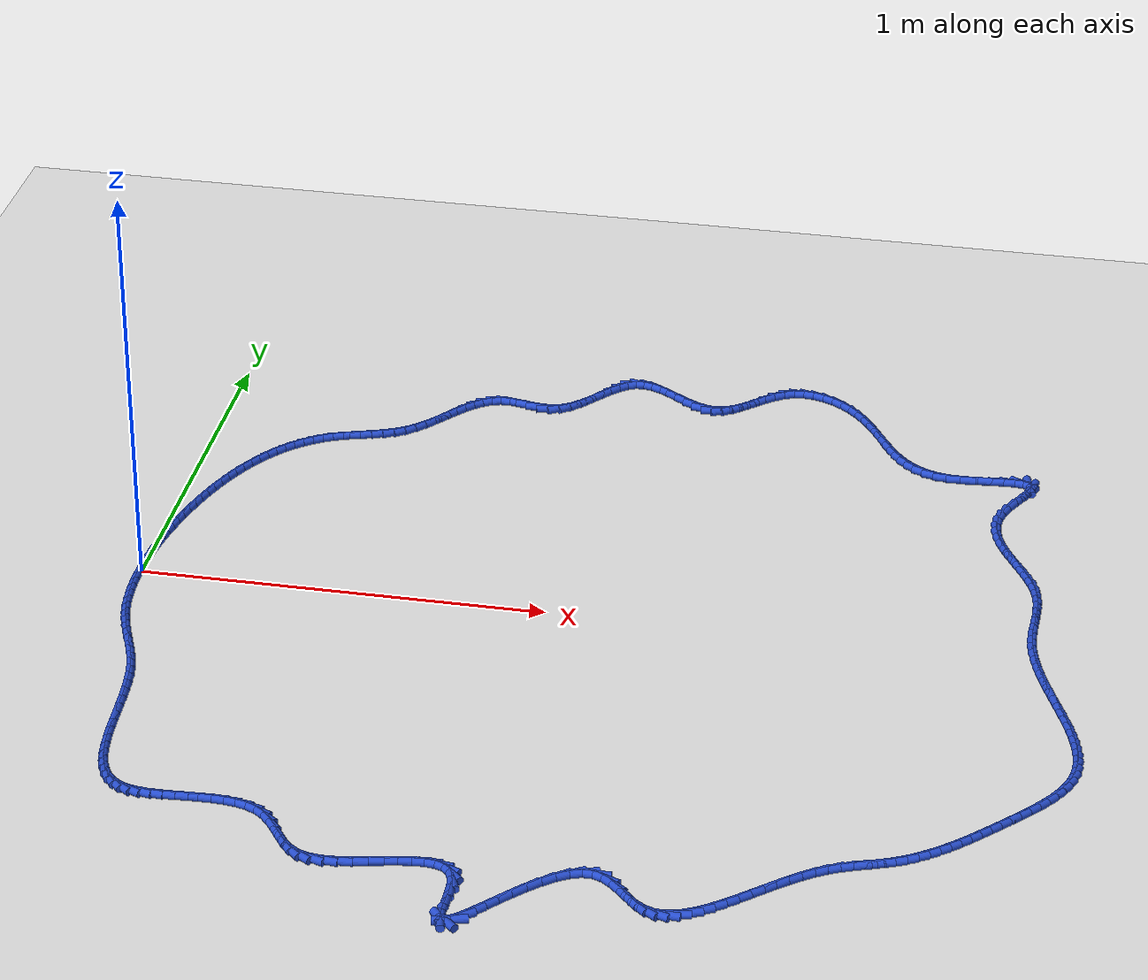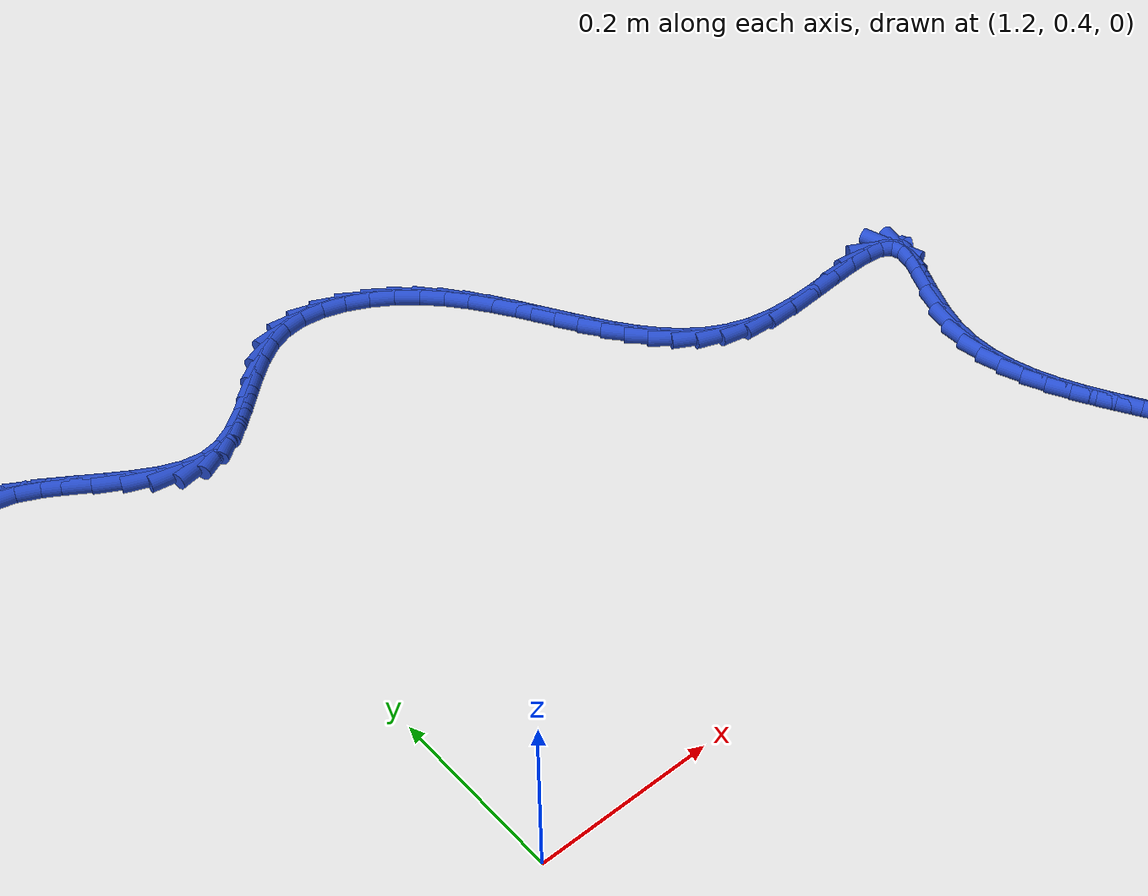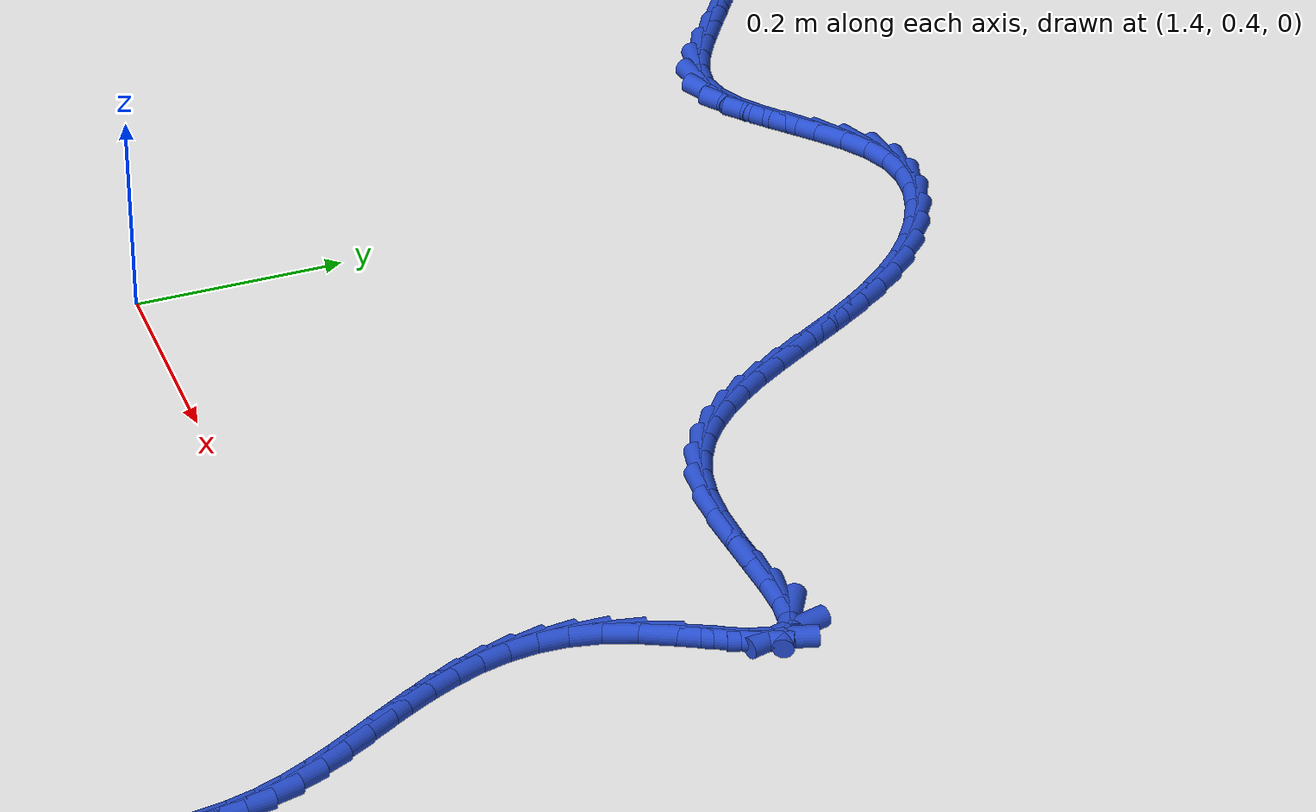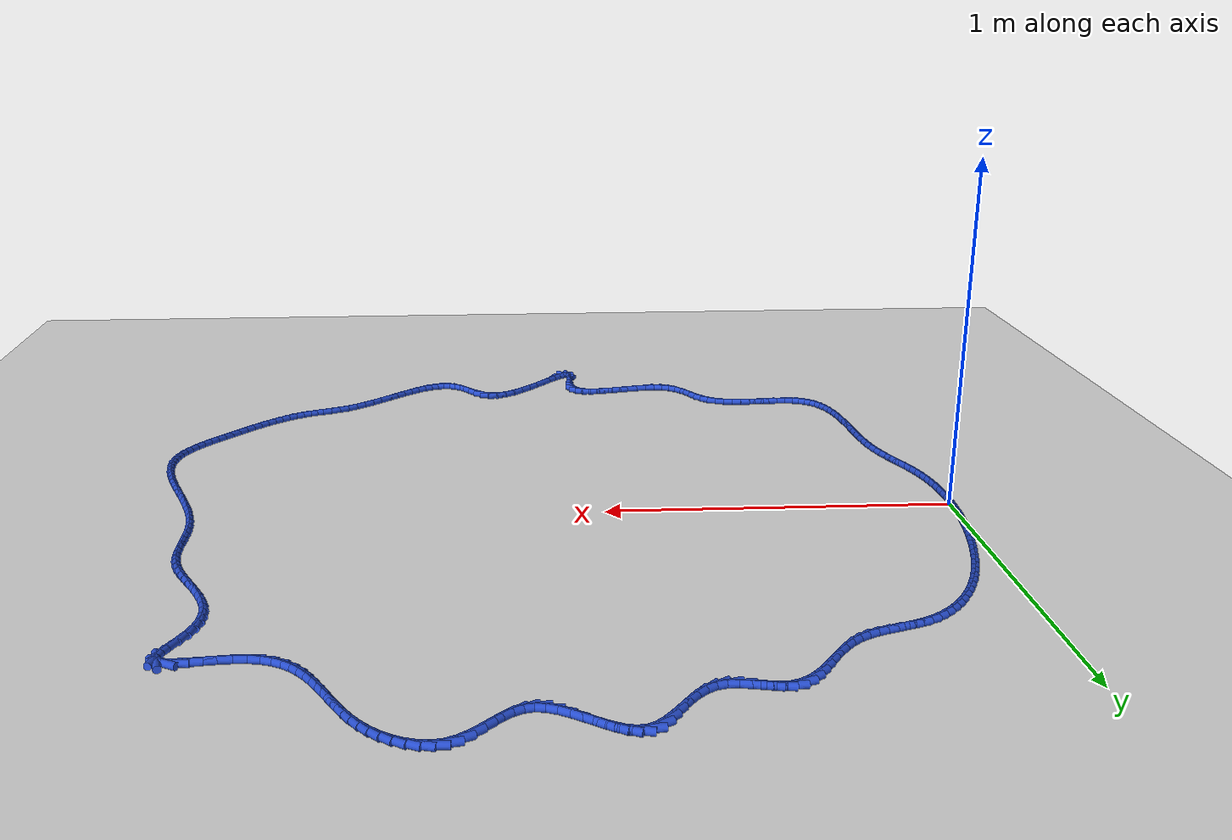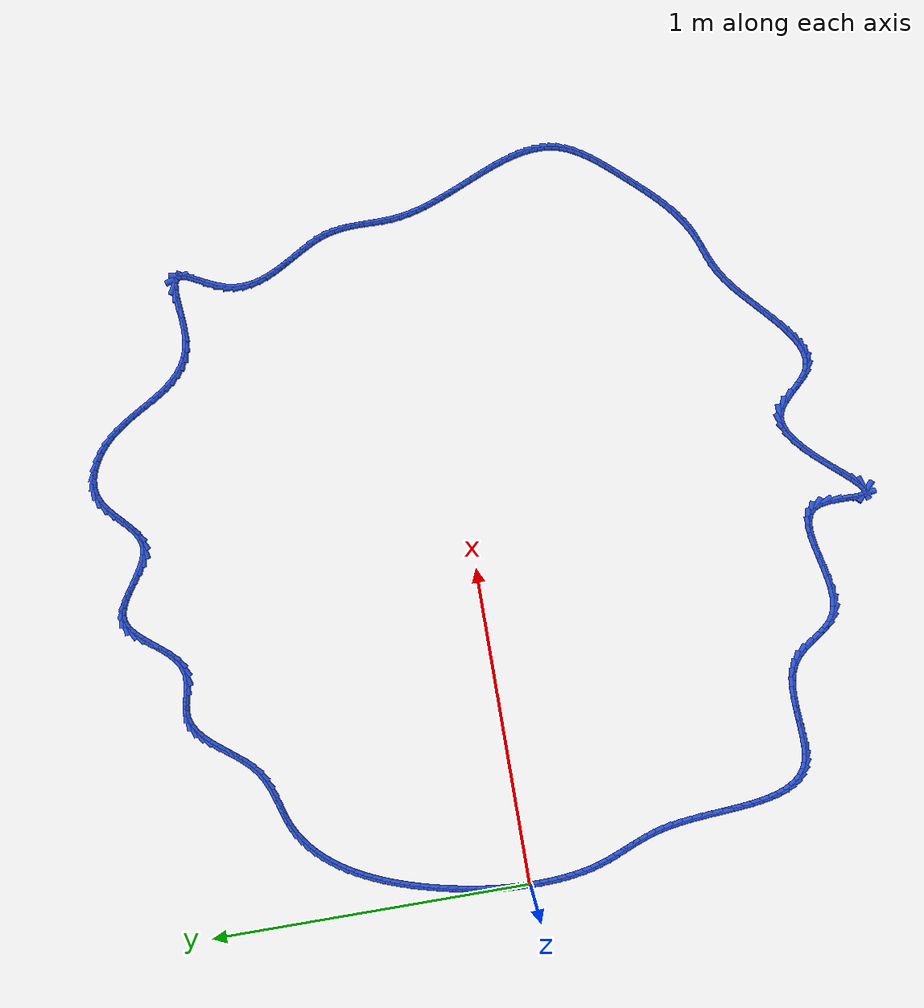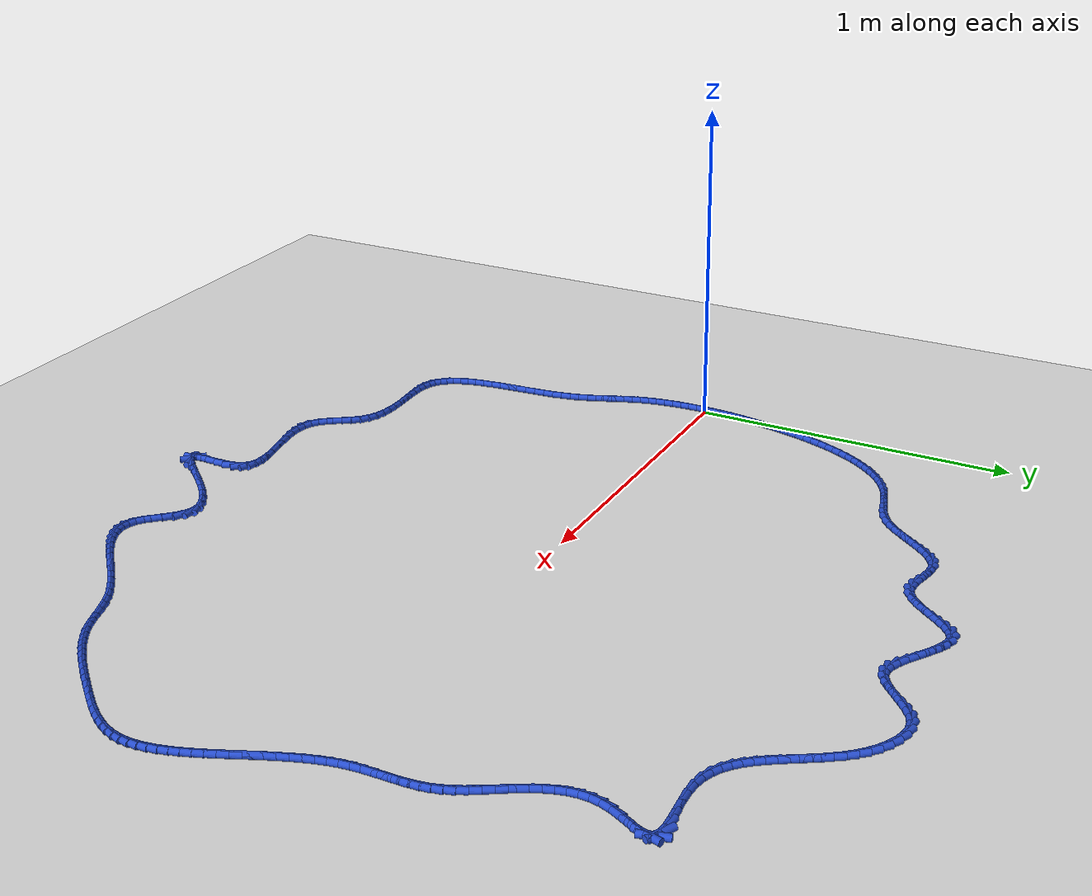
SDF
<sdf version="1.6">
 <world name="default">
  <light name="sun" type="directional">
   <pose>0 0 10 0 -0 0</pose>
   <diffuse>0.8 0.8 0.8 1</diffuse>
   <specular>0.2 0.2 0.2 1</specular>
   <attenuation>
    <range>1000</range>
    <constant>0.9</constant>
    <linear>0.01</linear>
    <quadratic>0.001</quadratic>
   </attenuation>
   <direction>-0.5 0.1 -0.9</direction>
  </light>
  <model name="ground_plane">
   <static>1</static>
   <link name="link">
    <collision name="collision">
     <geometry><plane><normal>0 0 1</normal><size>100 100</size></plane></geometry>
     <surface><friction><ode><mu>100</mu><mu2>50</mu2></ode></friction></surface>
    </collision>
    <visual name="visual">
     <cast_shadows>0</cast_shadows>
     <geometry><plane><normal>0 0 1</normal><size>100 100</size></plane></geometry>
     <material>
      <script><uri>file://media/materials/scripts/gazebo.material</uri><name>Gazebo/WhiteGlow</name></script>
     </material>
    </visual>
   </link>
  </model>
  <gravity>0 0 -9.8</gravity>
  <magnetic_field>6e-06 2.3e-05 -4.2e-05</magnetic_field>
  <atmosphere type="adiabatic"/>
  <physics name="default_physics" default="0" type="ode">
   <max_step_size>0.001</max_step_size>
   <real_time_factor>1</real_time_factor>
   <real_time_update_rate>1000</real_time_update_rate>
  </physics>
  <scene><ambient>0.4 0.4 0.4 1</ambient><background>0.7 0.7 0.7 1</background><shadows>1</shadows></scene>
  <spherical_coordinates>
   <surface_model>EARTH_WGS84</surface_model>
   <latitude_deg>0</latitude_deg>
   <longitude_deg>0</longitude_deg>
   <elevation>0</elevation>
   <heading_deg>0</heading_deg>
  </spherical_coordinates>
  <model name="line">
   <link name="link_0">
    <pose>0.0 0.0 0.01 0 1.57 1.5403007521404364</pose>
    <collision name="collision">
     <geometry><cylinder><radius>0.01</radius><length>0.08</length></cylinder></geometry>
    </collision>
    <visual name="visual">
     <material>
      <script><name>Gazebo/Blue</name><uri>file://media/materials/scripts/gazebo.material</uri></script>
     </material>
     <geometry><cylinder><radius>0.01</radius><length>0.08</length></cylinder></geometry>
    </visual>
   </link>
   <link name="link_1">
    <pose>0.0008429384960956971 0.02763276915116524 0.01 0 1.57 1.5160550999195674</pose>
    <collision name="collision">
     <geometry><cylinder><radius>0.01</radius><length>0.08</length></cylinder></geometry>
    </collision>
    <visual name="visual">
     <material>
      <script><name>Gazebo/Blue</name><uri>file://media/materials/scripts/gazebo.material</uri></script>
     </material>
     <geometry><cylinder><radius>0.01</radius><length>0.08</length></cylinder></geometry>
    </visual>
   </link>
   <link name="link_2">
    <pose>0.002346321804139864 0.05506878791171287 0.01 0 1.57 1.4921455673835677</pose>
    <collision name="collision">
     <geometry><cylinder><radius>0.01</radius><length>0.08</length></cylinder></geometry>
    </collision>
    <visual name="visual">
     <material>
      <script><name>Gazebo/Blue</name><uri>file://media/materials/scripts/gazebo.material</uri></script>
     </material>
     <geometry><cylinder><radius>0.01</radius><length>0.08</length></cylinder></geometry>
    </visual>
   </link>
   <link name="link_3">
    <pose>0.004500088033579795 0.08239622109470944 0.01 0 1.57 1.4688299530244748</pose>
    <collision name="collision">
     <geometry><cylinder><radius>0.01</radius><length>0.08</length></cylinder></geometry>
    </collision>
    <visual name="visual">
     <material>
      <script><name>Gazebo/Blue</name><uri>file://media/materials/scripts/gazebo.material</uri></script>
     </material>
     <geometry><cylinder><radius>0.01</radius><length>0.08</length></cylinder></geometry>
    </visual>
   </link>
   <link name="link_4">
    <pose>0.007294175293862791 0.10970323351322152 0.01 0 1.57 1.4463513469876295</pose>
    <collision name="collision">
     <geometry><cylinder><radius>0.01</radius><length>0.08</length></cylinder></geometry>
    </collision>
    <visual name="visual">
     <material>
      <script><name>Gazebo/Blue</name><uri>file://media/materials/scripts/gazebo.material</uri></script>
     </material>
     <geometry><cylinder><radius>0.01</radius><length>0.08</length></cylinder></geometry>
    </visual>
   </link>
   <link name="link_5">
    <pose>0.010718521694436146 0.13707798998031562 0.01 0 1.57 1.4249292615594318</pose>
    <collision name="collision">
     <geometry><cylinder><radius>0.01</radius><length>0.08</length></cylinder></geometry>
    </collision>
    <visual name="visual">
     <material>
      <script><name>Gazebo/Blue</name><uri>file://media/materials/scripts/gazebo.material</uri></script>
     </material>
     <geometry><cylinder><radius>0.01</radius><length>0.08</length></cylinder></geometry>
    </visual>
   </link>
   <link name="link_6">
    <pose>0.01476306534474716 0.16460865530905835 0.01 0 1.57 1.4047525400629095</pose>
    <collision name="collision">
     <geometry><cylinder><radius>0.01</radius><length>0.08</length></cylinder></geometry>
    </collision>
    <visual name="visual">
     <material>
      <script><name>Gazebo/Blue</name><uri>file://media/materials/scripts/gazebo.material</uri></script>
     </material>
     <geometry><cylinder><radius>0.01</radius><length>0.08</length></cylinder></geometry>
    </visual>
   </link>
   <link name="link_7">
    <pose>0.019417744354243125 0.19238339431251622 0.01 0 1.57 1.385974489542087</pose>
    <collision name="collision">
     <geometry><cylinder><radius>0.01</radius><length>0.08</length></cylinder></geometry>
    </collision>
    <visual name="visual">
     <material>
      <script><name>Gazebo/Blue</name><uri>file://media/materials/scripts/gazebo.material</uri></script>
     </material>
     <geometry><cylinder><radius>0.01</radius><length>0.08</length></cylinder></geometry>
    </visual>
   </link>
   <link name="link_8">
    <pose>0.024672496832371348 0.22049037180375586 0.01 0 1.57 1.3683050096618266</pose>
    <collision name="collision">
     <geometry><cylinder><radius>0.01</radius><length>0.08</length></cylinder></geometry>
    </collision>
    <visual name="visual">
     <material>
      <script><name>Gazebo/Blue</name><uri>file://media/materials/scripts/gazebo.material</uri></script>
     </material>
     <geometry><cylinder><radius>0.01</radius><length>0.08</length></cylinder></geometry>
    </visual>
   </link>
   <link name="link_9">
    <pose>0.030523401681201965 0.24898896514108323 0.01 0 1.57 1.3497427687739518</pose>
    <collision name="collision">
     <geometry><cylinder><radius>0.01</radius><length>0.08</length></cylinder></geometry>
    </collision>
    <visual name="visual">
     <material>
      <script><name>Gazebo/Blue</name><uri>file://media/materials/scripts/gazebo.material</uri></script>
     </material>
     <geometry><cylinder><radius>0.01</radius><length>0.08</length></cylinder></geometry>
    </visual>
   </link>
   <link name="link_10">
    <pose>0.03699701584726615 0.27779567349427137 0.01 0 1.57 1.3295372013325133</pose>
    <collision name="collision">
     <geometry><cylinder><radius>0.01</radius><length>0.08</length></cylinder></geometry>
    </collision>
    <visual name="visual">
     <material>
      <script><name>Gazebo/Blue</name><uri>file://media/materials/scripts/gazebo.material</uri></script>
     </material>
     <geometry><cylinder><radius>0.01</radius><length>0.08</length></cylinder></geometry>
    </visual>
   </link>
   <link name="link_11">
    <pose>0.04412933418608833 0.30678275200876887 0.01 0 1.57 1.307524137213897</pose>
    <collision name="collision">
     <geometry><cylinder><radius>0.01</radius><length>0.08</length></cylinder></geometry>
    </collision>
    <visual name="visual">
     <material>
      <script><name>Gazebo/Blue</name><uri>file://media/materials/scripts/gazebo.material</uri></script>
     </material>
     <geometry><cylinder><radius>0.01</radius><length>0.08</length></cylinder></geometry>
    </visual>
   </link>
   <link name="link_12">
    <pose>0.05195635438358558 0.335822442561411 0.01 0 1.57 1.2835144472038014</pose>
    <collision name="collision">
     <geometry><cylinder><radius>0.01</radius><length>0.08</length></cylinder></geometry>
    </collision>
    <visual name="visual">
     <material>
      <script><name>Gazebo/Blue</name><uri>file://media/materials/scripts/gazebo.material</uri></script>
     </material>
     <geometry><cylinder><radius>0.01</radius><length>0.08</length></cylinder></geometry>
    </visual>
   </link>
   <link name="link_13">
    <pose>0.060514074125675 0.3647869870290334 0.01 0 1.57 1.2572915305209686</pose>
    <collision name="collision">
     <geometry><cylinder><radius>0.01</radius><length>0.08</length></cylinder></geometry>
    </collision>
    <visual name="visual">
     <material>
      <script><name>Gazebo/Blue</name><uri>file://media/materials/scripts/gazebo.material</uri></script>
     </material>
     <geometry><cylinder><radius>0.01</radius><length>0.08</length></cylinder></geometry>
    </visual>
   </link>
   <link name="link_14">
    <pose>0.06983849109827363 0.39354862728847173 0.01 0 1.57 1.2286089115119978</pose>
    <collision name="collision">
     <geometry><cylinder><radius>0.01</radius><length>0.08</length></cylinder></geometry>
    </collision>
    <visual name="visual">
     <material>
      <script><name>Gazebo/Blue</name><uri>file://media/materials/scripts/gazebo.material</uri></script>
     </material>
     <geometry><cylinder><radius>0.01</radius><length>0.08</length></cylinder></geometry>
    </visual>
   </link>
   <link name="link_15">
    <pose>0.0799656029872986 0.4219796052165614 0.01 0 1.57 1.1971880550110687</pose>
    <collision name="collision">
     <geometry><cylinder><radius>0.01</radius><length>0.08</length></cylinder></geometry>
    </collision>
    <visual name="visual">
     <material>
      <script><name>Gazebo/Blue</name><uri>file://media/materials/scripts/gazebo.material</uri></script>
     </material>
     <geometry><cylinder><radius>0.01</radius><length>0.08</length></cylinder></geometry>
    </visual>
   </link>
   <link name="link_16">
    <pose>0.09093140747866699 0.4499521626901382 0.01 0 1.57 1.1627168600469073</pose>
    <collision name="collision">
     <geometry><cylinder><radius>0.01</radius><length>0.08</length></cylinder></geometry>
    </collision>
    <visual name="visual">
     <material>
      <script><name>Gazebo/Blue</name><uri>file://media/materials/scripts/gazebo.material</uri></script>
     </material>
     <geometry><cylinder><radius>0.01</radius><length>0.08</length></cylinder></geometry>
    </visual>
   </link>
   <link name="link_17">
    <pose>0.1027719022582958 0.47733854158603733 0.01 0 1.57 1.124849536209441</pose>
    <collision name="collision">
     <geometry><cylinder><radius>0.01</radius><length>0.08</length></cylinder></geometry>
    </collision>
    <visual name="visual">
     <material>
      <script><name>Gazebo/Blue</name><uri>file://media/materials/scripts/gazebo.material</uri></script>
     </material>
     <geometry><cylinder><radius>0.01</radius><length>0.08</length></cylinder></geometry>
    </visual>
   </link>
   <link name="link_18">
    <pose>0.11552308501210215 0.5040109837810945 0.01 0 1.57 1.0832089118174744</pose>
    <collision name="collision">
     <geometry><cylinder><radius>0.01</radius><length>0.08</length></cylinder></geometry>
    </collision>
    <visual name="visual">
     <material>
      <script><name>Gazebo/Blue</name><uri>file://media/materials/scripts/gazebo.material</uri></script>
     </material>
     <geometry><cylinder><radius>0.01</radius><length>0.08</length></cylinder></geometry>
    </visual>
   </link>
   <link name="link_19">
    <pose>0.12922095342600318 0.5298417311521454 0.01 0 1.57 1.037392675830754</pose>
    <collision name="collision">
     <geometry><cylinder><radius>0.01</radius><length>0.08</length></cylinder></geometry>
    </collision>
    <visual name="visual">
     <material>
      <script><name>Gazebo/Blue</name><uri>file://media/materials/scripts/gazebo.material</uri></script>
     </material>
     <geometry><cylinder><radius>0.01</radius><length>0.08</length></cylinder></geometry>
    </visual>
   </link>
   <link name="link_20">
    <pose>0.14390150518591585 0.5547030255760252 0.01 0 1.57 0.98698559013131</pose>
    <collision name="collision">
     <geometry><cylinder><radius>0.01</radius><length>0.08</length></cylinder></geometry>
    </collision>
    <visual name="visual">
     <material>
      <script><name>Gazebo/Blue</name><uri>file://media/materials/scripts/gazebo.material</uri></script>
     </material>
     <geometry><cylinder><radius>0.01</radius><length>0.08</length></cylinder></geometry>
    </visual>
   </link>
   <link name="link_21">
    <pose>0.15960073797775734 0.57846710892957 0.01 0 1.57 0.9315802237671242</pose>
    <collision name="collision">
     <geometry><cylinder><radius>0.01</radius><length>0.08</length></cylinder></geometry>
    </collision>
    <visual name="visual">
     <material>
      <script><name>Gazebo/Blue</name><uri>file://media/materials/scripts/gazebo.material</uri></script>
     </material>
     <geometry><cylinder><radius>0.01</radius><length>0.08</length></cylinder></geometry>
    </visual>
   </link>
   <link name="link_22">
    <pose>0.17635464948744473 0.6010062230896149 0.01 0 1.57 0.8708090156658082</pose>
    <collision name="collision">
     <geometry><cylinder><radius>0.01</radius><length>0.08</length></cylinder></geometry>
    </collision>
    <visual name="visual">
     <material>
      <script><name>Gazebo/Blue</name><uri>file://media/materials/scripts/gazebo.material</uri></script>
     </material>
     <geometry><cylinder><radius>0.01</radius><length>0.08</length></cylinder></geometry>
    </visual>
   </link>
   <link name="link_23">
    <pose>0.194199237400895 0.6221926099329959 0.01 0 1.57 0.8043900182225887</pose>
    <collision name="collision">
     <geometry><cylinder><radius>0.01</radius><length>0.08</length></cylinder></geometry>
    </collision>
    <visual name="visual">
     <material>
      <script><name>Gazebo/Blue</name><uri>file://media/materials/scripts/gazebo.material</uri></script>
     </material>
     <geometry><cylinder><radius>0.01</radius><length>0.08</length></cylinder></geometry>
    </visual>
   </link>
   <link name="link_24">
    <pose>0.21317049940402527 0.6418985113365477 0.01 0 1.57 0.7321868368173543</pose>
    <collision name="collision">
     <geometry><cylinder><radius>0.01</radius><length>0.08</length></cylinder></geometry>
    </collision>
    <visual name="visual">
     <material>
      <script><name>Gazebo/Blue</name><uri>file://media/materials/scripts/gazebo.material</uri></script>
     </material>
     <geometry><cylinder><radius>0.01</radius><length>0.08</length></cylinder></geometry>
    </visual>
   </link>
   <link name="link_25">
    <pose>0.23330443318275274 0.6599961691771069 0.01 0 1.57 0.6542793305869732</pose>
    <collision name="collision">
     <geometry><cylinder><radius>0.01</radius><length>0.08</length></cylinder></geometry>
    </collision>
    <visual name="visual">
     <material>
      <script><name>Gazebo/Blue</name><uri>file://media/materials/scripts/gazebo.material</uri></script>
     </material>
     <geometry><cylinder><radius>0.01</radius><length>0.08</length></cylinder></geometry>
    </visual>
   </link>
   <link name="link_26">
    <pose>0.2546370364229943 0.6763578253315083 0.01 0 1.57 0.5710353343384427</pose>
    <collision name="collision">
     <geometry><cylinder><radius>0.01</radius><length>0.08</length></cylinder></geometry>
    </collision>
    <visual name="visual">
     <material>
      <script><name>Gazebo/Blue</name><uri>file://media/materials/scripts/gazebo.material</uri></script>
     </material>
     <geometry><cylinder><radius>0.01</radius><length>0.08</length></cylinder></geometry>
    </visual>
   </link>
   <link name="link_27">
    <pose>0.277204306810667 0.6908557216765876 0.01 0 1.57 0.4831661951304047</pose>
    <collision name="collision">
     <geometry><cylinder><radius>0.01</radius><length>0.08</length></cylinder></geometry>
    </collision>
    <visual name="visual">
     <material>
      <script><name>Gazebo/Blue</name><uri>file://media/materials/scripts/gazebo.material</uri></script>
     </material>
     <geometry><cylinder><radius>0.01</radius><length>0.08</length></cylinder></geometry>
    </visual>
   </link>
   <link name="link_28">
    <pose>0.30104224203168817 0.7033621000891808 0.01 0 1.57 0.3944288428541046</pose>
    <collision name="collision">
     <geometry><cylinder><radius>0.01</radius><length>0.08</length></cylinder></geometry>
    </collision>
    <visual name="visual">
     <material>
      <script><name>Gazebo/Blue</name><uri>file://media/materials/scripts/gazebo.material</uri></script>
     </material>
     <geometry><cylinder><radius>0.01</radius><length>0.08</length></cylinder></geometry>
    </visual>
   </link>
   <link name="link_29">
    <pose>0.3261543498322696 0.7138148029819906 0.01 0 1.57 0.33050395442711866</pose>
    <collision name="collision">
     <geometry><cylinder><radius>0.01</radius><length>0.08</length></cylinder></geometry>
    </collision>
    <visual name="visual">
     <material>
      <script><name>Gazebo/Blue</name><uri>file://media/materials/scripts/gazebo.material</uri></script>
     </material>
     <geometry><cylinder><radius>0.01</radius><length>0.08</length></cylinder></geometry>
    </visual>
   </link>
   <link name="link_30">
    <pose>0.3522405422709018 0.7227646637422352 0.01 0 1.57 0.3036182680935461</pose>
    <collision name="collision">
     <geometry><cylinder><radius>0.01</radius><length>0.08</length></cylinder></geometry>
    </collision>
    <visual name="visual">
     <material>
      <script><name>Gazebo/Blue</name><uri>file://media/materials/scripts/gazebo.material</uri></script>
     </material>
     <geometry><cylinder><radius>0.01</radius><length>0.08</length></cylinder></geometry>
    </visual>
   </link>
   <link name="link_31">
    <pose>0.37883512808935776 0.7310968859165338 0.01 0 1.57 0.312417065026623</pose>
    <collision name="collision">
     <geometry><cylinder><radius>0.01</radius><length>0.08</length></cylinder></geometry>
    </collision>
    <visual name="visual">
     <material>
      <script><name>Gazebo/Blue</name><uri>file://media/materials/scripts/gazebo.material</uri></script>
     </material>
     <geometry><cylinder><radius>0.01</radius><length>0.08</length></cylinder></geometry>
    </visual>
   </link>
   <link name="link_32">
    <pose>0.4054707446708365 0.7397000476966767 0.01 0 1.57 0.35656774255827295</pose>
    <collision name="collision">
     <geometry><cylinder><radius>0.01</radius><length>0.08</length></cylinder></geometry>
    </collision>
    <visual name="visual">
     <material>
      <script><name>Gazebo/Blue</name><uri>file://media/materials/scripts/gazebo.material</uri></script>
     </material>
     <geometry><cylinder><radius>0.01</radius><length>0.08</length></cylinder></geometry>
    </visual>
   </link>
   <link name="link_33">
    <pose>0.4316800293985362 0.7494627272744537 0.01 0 1.57 0.43652444065668683</pose>
    <collision name="collision">
     <geometry><cylinder><radius>0.01</radius><length>0.08</length></cylinder></geometry>
    </collision>
    <visual name="visual">
     <material>
      <script><name>Gazebo/Blue</name><uri>file://media/materials/scripts/gazebo.material</uri></script>
     </material>
     <geometry><cylinder><radius>0.01</radius><length>0.08</length></cylinder></geometry>
    </visual>
   </link>
   <link name="link_34">
    <pose>0.4569956196556561 0.761273502841655 0.01 0 1.57 0.5518426479296237</pose>
    <collision name="collision">
     <geometry><cylinder><radius>0.01</radius><length>0.08</length></cylinder></geometry>
    </collision>
    <visual name="visual">
     <material>
      <script><name>Gazebo/Blue</name><uri>file://media/materials/scripts/gazebo.material</uri></script>
     </material>
     <geometry><cylinder><radius>0.01</radius><length>0.08</length></cylinder></geometry>
    </visual>
   </link>
   <link name="link_35">
    <pose>0.48095015282539455 0.7760209525900705 0.01 0 1.57 0.6901159250711582</pose>
    <collision name="collision">
     <geometry><cylinder><radius>0.01</radius><length>0.08</length></cylinder></geometry>
    </collision>
    <visual name="visual">
     <material>
      <script><name>Gazebo/Blue</name><uri>file://media/materials/scripts/gazebo.material</uri></script>
     </material>
     <geometry><cylinder><radius>0.01</radius><length>0.08</length></cylinder></geometry>
    </visual>
   </link>
   <link name="link_36">
    <pose>0.5031778902909975 0.7943706392566041 0.01 0 1.57 0.8005125224158287</pose>
    <collision name="collision">
     <geometry><cylinder><radius>0.01</radius><length>0.08</length></cylinder></geometry>
    </collision>
    <visual name="visual">
     <material>
      <script><name>Gazebo/Blue</name><uri>file://media/materials/scripts/gazebo.material</uri></script>
     </material>
     <geometry><cylinder><radius>0.01</radius><length>0.08</length></cylinder></geometry>
    </visual>
   </link>
   <link name="link_37">
    <pose>0.523891112528178 0.8157196536544086 0.01 0 1.57 0.8710023529055432</pose>
    <collision name="collision">
     <geometry><cylinder><radius>0.01</radius><length>0.08</length></cylinder></geometry>
    </collision>
    <visual name="visual">
     <material>
      <script><name>Gazebo/Blue</name><uri>file://media/materials/scripts/gazebo.material</uri></script>
     </material>
     <geometry><cylinder><radius>0.01</radius><length>0.08</length></cylinder></geometry>
    </visual>
   </link>
   <link name="link_38">
    <pose>0.5435061822806708 0.8390172248728707 0.01 0 1.57 0.9067907898642227</pose>
    <collision name="collision">
     <geometry><cylinder><radius>0.01</radius><length>0.08</length></cylinder></geometry>
    </collision>
    <visual name="visual">
     <material>
      <script><name>Gazebo/Blue</name><uri>file://media/materials/scripts/gazebo.material</uri></script>
     </material>
     <geometry><cylinder><radius>0.01</radius><length>0.08</length></cylinder></geometry>
    </visual>
   </link>
   <link name="link_39">
    <pose>0.5624396948482869 0.8632120716534369 0.01 0 1.57 0.9105280704576324</pose>
    <collision name="collision">
     <geometry><cylinder><radius>0.01</radius><length>0.08</length></cylinder></geometry>
    </collision>
    <visual name="visual">
     <material>
      <script><name>Gazebo/Blue</name><uri>file://media/materials/scripts/gazebo.material</uri></script>
     </material>
     <geometry><cylinder><radius>0.01</radius><length>0.08</length></cylinder></geometry>
    </visual>
   </link>
   <link name="link_40">
    <pose>0.581108245530838 0.887252912737553 0.01 0 1.57 0.8814954206568492</pose>
    <collision name="collision">
     <geometry><cylinder><radius>0.01</radius><length>0.08</length></cylinder></geometry>
    </collision>
    <visual name="visual">
     <material>
      <script><name>Gazebo/Blue</name><uri>file://media/materials/scripts/gazebo.material</uri></script>
     </material>
     <geometry><cylinder><radius>0.01</radius><length>0.08</length></cylinder></geometry>
    </visual>
   </link>
   <link name="link_41">
    <pose>0.5999284296281353 0.9100884668666653 0.01 0 1.57 0.8151779632568479</pose>
    <collision name="collision">
     <geometry><cylinder><radius>0.01</radius><length>0.08</length></cylinder></geometry>
    </collision>
    <visual name="visual">
     <material>
      <script><name>Gazebo/Blue</name><uri>file://media/materials/scripts/gazebo.material</uri></script>
     </material>
     <geometry><cylinder><radius>0.01</radius><length>0.08</length></cylinder></geometry>
    </visual>
   </link>
   <link name="link_42">
    <pose>0.61931684243999 0.9306674527822195 0.01 0 1.57 0.703178516138689</pose>
    <collision name="collision">
     <geometry><cylinder><radius>0.01</radius><length>0.08</length></cylinder></geometry>
    </collision>
    <visual name="visual">
     <material>
      <script><name>Gazebo/Blue</name><uri>file://media/materials/scripts/gazebo.material</uri></script>
     </material>
     <geometry><cylinder><radius>0.01</radius><length>0.08</length></cylinder></geometry>
    </visual>
   </link>
   <link name="link_43">
    <pose>0.6396900792662135 0.947938589225662 0.01 0 1.57 0.5352441282044931</pose>
    <collision name="collision">
     <geometry><cylinder><radius>0.01</radius><length>0.08</length></cylinder></geometry>
    </collision>
    <visual name="visual">
     <material>
      <script><name>Gazebo/Blue</name><uri>file://media/materials/scripts/gazebo.material</uri></script>
     </material>
     <geometry><cylinder><radius>0.01</radius><length>0.08</length></cylinder></geometry>
    </visual>
   </link>
   <link name="link_44">
    <pose>0.6614647354066171 0.9608505949384388 0.01 0 1.57 0.30785396486006</pose>
    <collision name="collision">
     <geometry><cylinder><radius>0.01</radius><length>0.08</length></cylinder></geometry>
    </collision>
    <visual name="visual">
     <material>
      <script><name>Gazebo/Blue</name><uri>file://media/materials/scripts/gazebo.material</uri></script>
     </material>
     <geometry><cylinder><radius>0.01</radius><length>0.08</length></cylinder></geometry>
    </visual>
   </link>
   <link name="link_45">
    <pose>0.6850574061610122 0.9683521886619961 0.01 0 1.57 0.04581799291284897</pose>
    <collision name="collision">
     <geometry><cylinder><radius>0.01</radius><length>0.08</length></cylinder></geometry>
    </collision>
    <visual name="visual">
     <material>
      <script><name>Gazebo/Blue</name><uri>file://media/materials/scripts/gazebo.material</uri></script>
     </material>
     <geometry><cylinder><radius>0.01</radius><length>0.08</length></cylinder></geometry>
    </visual>
   </link>
   <link name="link_46">
    <pose>0.7108379055784364 0.9695342266636289 0.01 0 1.57 -0.13747005656121272</pose>
    <collision name="collision">
     <geometry><cylinder><radius>0.01</radius><length>0.08</length></cylinder></geometry>
    </collision>
    <visual name="visual">
     <material>
      <script><name>Gazebo/Blue</name><uri>file://media/materials/scripts/gazebo.material</uri></script>
     </material>
     <geometry><cylinder><radius>0.01</radius><length>0.08</length></cylinder></geometry>
    </visual>
   </link>
   <link name="link_47">
    <pose>0.7384428450798773 0.9657152869105369 0.01 0 1.57 -0.19862703624959369</pose>
    <collision name="collision">
     <geometry><cylinder><radius>0.01</radius><length>0.08</length></cylinder></geometry>
    </collision>
    <visual name="visual">
     <material>
      <script><name>Gazebo/Blue</name><uri>file://media/materials/scripts/gazebo.material</uri></script>
     </material>
     <geometry><cylinder><radius>0.01</radius><length>0.08</length></cylinder></geometry>
    </visual>
   </link>
   <link name="link_48">
    <pose>0.7669269292275487 0.9599819804988537 0.01 0 1.57 -0.1575598486067952</pose>
    <collision name="collision">
     <geometry><cylinder><radius>0.01</radius><length>0.08</length></cylinder></geometry>
    </collision>
    <visual name="visual">
     <material>
      <script><name>Gazebo/Blue</name><uri>file://media/materials/scripts/gazebo.material</uri></script>
     </material>
     <geometry><cylinder><radius>0.01</radius><length>0.08</length></cylinder></geometry>
    </visual>
   </link>
   <link name="link_49">
    <pose>0.7953288480379348 0.9554695762213317 0.01 0 1.57 -0.005710546083951805</pose>
    <collision name="collision">
     <geometry><cylinder><radius>0.01</radius><length>0.08</length></cylinder></geometry>
    </collision>
    <visual name="visual">
     <material>
      <script><name>Gazebo/Blue</name><uri>file://media/materials/scripts/gazebo.material</uri></script>
     </material>
     <geometry><cylinder><radius>0.01</radius><length>0.08</length></cylinder></geometry>
    </visual>
   </link>
   <link name="link_50">
    <pose>0.8226872915275207 0.9553133428707214 0.01 0 1.57 0.27299837163486995</pose>
    <collision name="collision">
     <geometry><cylinder><radius>0.01</radius><length>0.08</length></cylinder></geometry>
    </collision>
    <visual name="visual">
     <material>
      <script><name>Gazebo/Blue</name><uri>file://media/materials/scripts/gazebo.material</uri></script>
     </material>
     <geometry><cylinder><radius>0.01</radius><length>0.08</length></cylinder></geometry>
    </visual>
   </link>
   <link name="link_51">
    <pose>0.8481011803756251 0.9624289486017513 0.01 0 1.57 0.5540703461499829</pose>
    <collision name="collision">
     <geometry><cylinder><radius>0.01</radius><length>0.08</length></cylinder></geometry>
    </collision>
    <visual name="visual">
     <material>
      <script><name>Gazebo/Blue</name><uri>file://media/materials/scripts/gazebo.material</uri></script>
     </material>
     <geometry><cylinder><radius>0.01</radius><length>0.08</length></cylinder></geometry>
    </visual>
   </link>
   <link name="link_52">
    <pose>0.87145253367265 0.9768768894256584 0.01 0 1.57 0.7403345087043823</pose>
    <collision name="collision">
     <geometry><cylinder><radius>0.01</radius><length>0.08</length></cylinder></geometry>
    </collision>
    <visual name="visual">
     <material>
      <script><name>Gazebo/Blue</name><uri>file://media/materials/scripts/gazebo.material</uri></script>
     </material>
     <geometry><cylinder><radius>0.01</radius><length>0.08</length></cylinder></geometry>
    </visual>
   </link>
   <link name="link_53">
    <pose>0.8931709753527252 0.9967210973544144 0.01 0 1.57 0.8478213494684496</pose>
    <collision name="collision">
     <geometry><cylinder><radius>0.01</radius><length>0.08</length></cylinder></geometry>
    </collision>
    <visual name="visual">
     <material>
      <script><name>Gazebo/Blue</name><uri>file://media/materials/scripts/gazebo.material</uri></script>
     </material>
     <geometry><cylinder><radius>0.01</radius><length>0.08</length></cylinder></geometry>
    </visual>
   </link>
   <link name="link_54">
    <pose>0.9136973639812348 1.0199845430013375 0.01 0 1.57 0.8957920718937642</pose>
    <collision name="collision">
     <geometry><cylinder><radius>0.01</radius><length>0.08</length></cylinder></geometry>
    </collision>
    <visual name="visual">
     <material>
      <script><name>Gazebo/Blue</name><uri>file://media/materials/scripts/gazebo.material</uri></script>
     </material>
     <geometry><cylinder><radius>0.01</radius><length>0.08</length></cylinder></geometry>
    </visual>
   </link>
   <link name="link_55">
    <pose>0.9334725581235639 1.0446901969797457 0.01 0 1.57 0.8928298519454283</pose>
    <collision name="collision">
     <geometry><cylinder><radius>0.01</radius><length>0.08</length></cylinder></geometry>
    </collision>
    <visual name="visual">
     <material>
      <script><name>Gazebo/Blue</name><uri>file://media/materials/scripts/gazebo.material</uri></script>
     </material>
     <geometry><cylinder><radius>0.01</radius><length>0.08</length></cylinder></geometry>
    </visual>
   </link>
   <link name="link_56">
    <pose>0.9529374163450962 1.0688610299029566 0.01 0 1.57 0.8353779203455667</pose>
    <collision name="collision">
     <geometry><cylinder><radius>0.01</radius><length>0.08</length></cylinder></geometry>
    </collision>
    <visual name="visual">
     <material>
      <script><name>Gazebo/Blue</name><uri>file://media/materials/scripts/gazebo.material</uri></script>
     </material>
     <geometry><cylinder><radius>0.01</radius><length>0.08</length></cylinder></geometry>
    </visual>
   </link>
   <link name="link_57">
    <pose>0.9725327972112167 1.090520012384289 0.01 0 1.57 0.7053097656562785</pose>
    <collision name="collision">
     <geometry><cylinder><radius>0.01</radius><length>0.08</length></cylinder></geometry>
    </collision>
    <visual name="visual">
     <material>
      <script><name>Gazebo/Blue</name><uri>file://media/materials/scripts/gazebo.material</uri></script>
     </material>
     <geometry><cylinder><radius>0.01</radius><length>0.08</length></cylinder></geometry>
    </visual>
   </link>
   <link name="link_58">
    <pose>0.9926995592873094 1.1076901150370606 0.01 0 1.57 0.46797052827440594</pose>
    <collision name="collision">
     <geometry><cylinder><radius>0.01</radius><length>0.08</length></cylinder></geometry>
    </collision>
    <visual name="visual">
     <material>
      <script><name>Gazebo/Blue</name><uri>file://media/materials/scripts/gazebo.material</uri></script>
     </material>
     <geometry><cylinder><radius>0.01</radius><length>0.08</length></cylinder></geometry>
    </visual>
   </link>
   <link name="link_59">
    <pose>1.013878561138759 1.118394308474589 0.01 0 1.57 0.10485933749303544</pose>
    <collision name="collision">
     <geometry><cylinder><radius>0.01</radius><length>0.08</length></cylinder></geometry>
    </collision>
    <visual name="visual">
     <material>
      <script><name>Gazebo/Blue</name><uri>file://media/materials/scripts/gazebo.material</uri></script>
     </material>
     <geometry><cylinder><radius>0.01</radius><length>0.08</length></cylinder></geometry>
    </visual>
   </link>
   <link name="link_60">
    <pose>1.0364882300027924 1.1207738712512638 0.01 0 1.57 -0.23254969838197154</pose>
    <collision name="collision">
     <geometry><cylinder><radius>0.01</radius><length>0.08</length></cylinder></geometry>
    </collision>
    <visual name="visual">
     <material>
      <script><name>Gazebo/Blue</name><uri>file://media/materials/scripts/gazebo.material</uri></script>
     </material>
     <geometry><cylinder><radius>0.01</radius><length>0.08</length></cylinder></geometry>
    </visual>
   </link>
   <link name="link_61">
    <pose>1.0605477566006232 1.1150757463689296 0.01 0 1.57 -0.4354573228581081</pose>
    <collision name="collision">
     <geometry><cylinder><radius>0.01</radius><length>0.08</length></cylinder></geometry>
    </collision>
    <visual name="visual">
     <material>
      <script><name>Gazebo/Blue</name><uri>file://media/materials/scripts/gazebo.material</uri></script>
     </material>
     <geometry><cylinder><radius>0.01</radius><length>0.08</length></cylinder></geometry>
    </visual>
   </link>
   <link name="link_62">
    <pose>1.0857328324228177 1.1033585701207203 0.01 0 1.57 -0.5413652199853947</pose>
    <collision name="collision">
     <geometry><cylinder><radius>0.01</radius><length>0.08</length></cylinder></geometry>
    </collision>
    <visual name="visual">
     <material>
      <script><name>Gazebo/Blue</name><uri>file://media/materials/scripts/gazebo.material</uri></script>
     </material>
     <geometry><cylinder><radius>0.01</radius><length>0.08</length></cylinder></geometry>
    </visual>
   </link>
   <link name="link_63">
    <pose>1.111707944161751 1.0877400754611395 0.01 0 1.57 -0.582279019685072</pose>
    <collision name="collision">
     <geometry><cylinder><radius>0.01</radius><length>0.08</length></cylinder></geometry>
    </collision>
    <visual name="visual">
     <material>
      <script><name>Gazebo/Blue</name><uri>file://media/materials/scripts/gazebo.material</uri></script>
     </material>
     <geometry><cylinder><radius>0.01</radius><length>0.08</length></cylinder></geometry>
    </visual>
   </link>
   <link name="link_64">
    <pose>1.1381375785097976 1.0703379953446925 0.01 0 1.57 -0.5713627301844789</pose>
    <collision name="collision">
     <geometry><cylinder><radius>0.01</radius><length>0.08</length></cylinder></geometry>
    </collision>
    <visual name="visual">
     <material>
      <script><name>Gazebo/Blue</name><uri>file://media/materials/scripts/gazebo.material</uri></script>
     </material>
     <geometry><cylinder><radius>0.01</radius><length>0.08</length></cylinder></geometry>
    </visual>
   </link>
   <link name="link_65">
    <pose>1.1646862221593333 1.0532700627258824 0.01 0 1.57 -0.5067236571244669</pose>
    <collision name="collision">
     <geometry><cylinder><radius>0.01</radius><length>0.08</length></cylinder></geometry>
    </collision>
    <visual name="visual">
     <material>
      <script><name>Gazebo/Blue</name><uri>file://media/materials/scripts/gazebo.material</uri></script>
     </material>
     <geometry><cylinder><radius>0.01</radius><length>0.08</length></cylinder></geometry>
    </visual>
   </link>
   <link name="link_66">
    <pose>1.1910183618027324 1.0386540105592135 0.01 0 1.57 -0.3715931306546923</pose>
    <collision name="collision">
     <geometry><cylinder><radius>0.01</radius><length>0.08</length></cylinder></geometry>
    </collision>
    <visual name="visual">
     <material>
      <script><name>Gazebo/Blue</name><uri>file://media/materials/scripts/gazebo.material</uri></script>
     </material>
     <geometry><cylinder><radius>0.01</radius><length>0.08</length></cylinder></geometry>
    </visual>
   </link>
   <link name="link_67">
    <pose>1.2167984841323702 1.0286075717991898 0.01 0 1.57 -0.13413319737967627</pose>
    <collision name="collision">
     <geometry><cylinder><radius>0.01</radius><length>0.08</length></cylinder></geometry>
    </collision>
    <visual name="visual">
     <material>
      <script><name>Gazebo/Blue</name><uri>file://media/materials/scripts/gazebo.material</uri></script>
     </material>
     <geometry><cylinder><radius>0.01</radius><length>0.08</length></cylinder></geometry>
    </visual>
   </link>
   <link name="link_68">
    <pose>1.2416910758406217 1.0252484794003158 0.01 0 1.57 0.20399295976134277</pose>
    <collision name="collision">
     <geometry><cylinder><radius>0.01</radius><length>0.08</length></cylinder></geometry>
    </collision>
    <visual name="visual">
     <material>
      <script><name>Gazebo/Blue</name><uri>file://media/materials/scripts/gazebo.material</uri></script>
     </material>
     <geometry><cylinder><radius>0.01</radius><length>0.08</length></cylinder></geometry>
    </visual>
   </link>
   <link name="link_69">
    <pose>1.2654495829845958 1.0301634127264439 0.01 0 1.57 0.4839980641135124</pose>
    <collision name="collision">
     <geometry><cylinder><radius>0.01</radius><length>0.08</length></cylinder></geometry>
    </collision>
    <visual name="visual">
     <material>
      <script><name>Gazebo/Blue</name><uri>file://media/materials/scripts/gazebo.material</uri></script>
     </material>
     <geometry><cylinder><radius>0.01</radius><length>0.08</length></cylinder></geometry>
    </visual>
   </link>
   <link name="link_70">
    <pose>1.2882910963571448 1.0421712683179045 0.01 0 1.57 0.6521079023328774</pose>
    <collision name="collision">
     <geometry><cylinder><radius>0.01</radius><length>0.08</length></cylinder></geometry>
    </collision>
    <visual name="visual">
     <material>
      <script><name>Gazebo/Blue</name><uri>file://media/materials/scripts/gazebo.material</uri></script>
     </material>
     <geometry><cylinder><radius>0.01</radius><length>0.08</length></cylinder></geometry>
    </visual>
   </link>
   <link name="link_71">
    <pose>1.3105832693853003 1.0591921410235174 0.01 0 1.57 0.7341628290892473</pose>
    <collision name="collision">
     <geometry><cylinder><radius>0.01</radius><length>0.08</length></cylinder></geometry>
    </collision>
    <visual name="visual">
     <material>
      <script><name>Gazebo/Blue</name><uri>file://media/materials/scripts/gazebo.material</uri></script>
     </material>
     <geometry><cylinder><radius>0.01</radius><length>0.08</length></cylinder></geometry>
    </visual>
   </link>
   <link name="link_72">
    <pose>1.3326938348922361 1.079145651727313 0.01 0 1.57 0.7508217838398705</pose>
    <collision name="collision">
     <geometry><cylinder><radius>0.01</radius><length>0.08</length></cylinder></geometry>
    </collision>
    <visual name="visual">
     <material>
      <script><name>Gazebo/Blue</name><uri>file://media/materials/scripts/gazebo.material</uri></script>
     </material>
     <geometry><cylinder><radius>0.01</radius><length>0.08</length></cylinder></geometry>
    </visual>
   </link>
   <link name="link_73">
    <pose>1.3549905257011259 1.0999514213133232 0.01 0 1.57 0.7084109012326739</pose>
    <collision name="collision">
     <geometry><cylinder><radius>0.01</radius><length>0.08</length></cylinder></geometry>
    </collision>
    <visual name="visual">
     <material>
      <script><name>Gazebo/Blue</name><uri>file://media/materials/scripts/gazebo.material</uri></script>
     </material>
     <geometry><cylinder><radius>0.01</radius><length>0.08</length></cylinder></geometry>
    </visual>
   </link>
   <link name="link_74">
    <pose>1.3778410746351433 1.1195290706655772 0.01 0 1.57 0.6001648621683521</pose>
    <collision name="collision">
     <geometry><cylinder><radius>0.01</radius><length>0.08</length></cylinder></geometry>
    </collision>
    <visual name="visual">
     <material>
      <script><name>Gazebo/Blue</name><uri>file://media/materials/scripts/gazebo.material</uri></script>
     </material>
     <geometry><cylinder><radius>0.01</radius><length>0.08</length></cylinder></geometry>
    </visual>
   </link>
   <link name="link_75">
    <pose>1.4016132145174631 1.1357982206681072 0.01 0 1.57 0.4095901310267011</pose>
    <collision name="collision">
     <geometry><cylinder><radius>0.01</radius><length>0.08</length></cylinder></geometry>
    </collision>
    <visual name="visual">
     <material>
      <script><name>Gazebo/Blue</name><uri>file://media/materials/scripts/gazebo.material</uri></script>
     </material>
     <geometry><cylinder><radius>0.01</radius><length>0.08</length></cylinder></geometry>
    </visual>
   </link>
   <link name="link_76">
    <pose>1.4266746741748833 1.1466785029190596 0.01 0 1.57 0.14798488247998606</pose>
    <collision name="collision">
     <geometry><cylinder><radius>0.01</radius><length>0.08</length></cylinder></geometry>
    </collision>
    <visual name="visual">
     <material>
      <script><name>Gazebo/Blue</name><uri>file://media/materials/scripts/gazebo.material</uri></script>
     </material>
     <geometry><cylinder><radius>0.01</radius><length>0.08</length></cylinder></geometry>
    </visual>
   </link>
   <link name="link_77">
    <pose>1.4531910620310113 1.1506314253849277 0.01 0 1.57 -0.09168752158299566</pose>
    <collision name="collision">
     <geometry><cylinder><radius>0.01</radius><length>0.08</length></cylinder></geometry>
    </collision>
    <visual name="visual">
     <material>
      <script><name>Gazebo/Blue</name><uri>file://media/materials/scripts/gazebo.material</uri></script>
     </material>
     <geometry><cylinder><radius>0.01</radius><length>0.08</length></cylinder></geometry>
    </visual>
   </link>
   <link name="link_78">
    <pose>1.4805841235058557 1.1481127617103806 0.01 0 1.57 -0.28543511425418</pose>
    <collision name="collision">
     <geometry><cylinder><radius>0.01</radius><length>0.08</length></cylinder></geometry>
    </collision>
    <visual name="visual">
     <material>
      <script><name>Gazebo/Blue</name><uri>file://media/materials/scripts/gazebo.material</uri></script>
     </material>
     <geometry><cylinder><radius>0.01</radius><length>0.08</length></cylinder></geometry>
    </visual>
   </link>
   <link name="link_79">
    <pose>1.5081045207154684 1.140036952740264 0.01 0 1.57 -0.4416807370855802</pose>
    <collision name="collision">
     <geometry><cylinder><radius>0.01</radius><length>0.08</length></cylinder></geometry>
    </collision>
    <visual name="visual">
     <material>
      <script><name>Gazebo/Blue</name><uri>file://media/materials/scripts/gazebo.material</uri></script>
     </material>
     <geometry><cylinder><radius>0.01</radius><length>0.08</length></cylinder></geometry>
    </visual>
   </link>
   <link name="link_80">
    <pose>1.5350029157759055 1.1273184393194247 0.01 0 1.57 -0.5723493183631833</pose>
    <collision name="collision">
     <geometry><cylinder><radius>0.01</radius><length>0.08</length></cylinder></geometry>
    </collision>
    <visual name="visual">
     <material>
      <script><name>Gazebo/Blue</name><uri>file://media/materials/scripts/gazebo.material</uri></script>
     </material>
     <geometry><cylinder><radius>0.01</radius><length>0.08</length></cylinder></geometry>
    </visual>
   </link>
   <link name="link_81">
    <pose>1.5605299708032205 1.110871662292709 0.01 0 1.57 -0.6884382442593434</pose>
    <collision name="collision">
     <geometry><cylinder><radius>0.01</radius><length>0.08</length></cylinder></geometry>
    </collision>
    <visual name="visual">
     <material>
      <script><name>Gazebo/Blue</name><uri>file://media/materials/scripts/gazebo.material</uri></script>
     </material>
     <geometry><cylinder><radius>0.01</radius><length>0.08</length></cylinder></geometry>
    </visual>
   </link>
   <link name="link_82">
    <pose>1.5839458589698256 1.0916070858261908 0.01 0 1.57 -0.7934648081408842</pose>
    <collision name="collision">
     <geometry><cylinder><radius>0.01</radius><length>0.08</length></cylinder></geometry>
    </collision>
    <visual name="visual">
     <material>
      <script><name>Gazebo/Blue</name><uri>file://media/materials/scripts/gazebo.material</uri></script>
     </material>
     <geometry><cylinder><radius>0.01</radius><length>0.08</length></cylinder></geometry>
    </visual>
   </link>
   <link name="link_83">
    <pose>1.6049663762186324 1.07024467312244 0.01 0 1.57 -0.8808923579072564</pose>
    <collision name="collision">
     <geometry><cylinder><radius>0.01</radius><length>0.08</length></cylinder></geometry>
    </collision>
    <visual name="visual">
     <material>
      <script><name>Gazebo/Blue</name><uri>file://media/materials/scripts/gazebo.material</uri></script>
     </material>
     <geometry><cylinder><radius>0.01</radius><length>0.08</length></cylinder></geometry>
    </visual>
   </link>
   <link name="link_84">
    <pose>1.6239543033740718 1.0472338757869752 0.01 0 1.57 -0.9489089492983109</pose>
    <collision name="collision">
     <geometry><cylinder><radius>0.01</radius><length>0.08</length></cylinder></geometry>
    </collision>
    <visual name="visual">
     <material>
      <script><name>Gazebo/Blue</name><uri>file://media/materials/scripts/gazebo.material</uri></script>
     </material>
     <geometry><cylinder><radius>0.01</radius><length>0.08</length></cylinder></geometry>
    </visual>
   </link>
   <link name="link_85">
    <pose>1.6413216860974906 1.0230035472473766 0.01 0 1.57 -0.997370352363694</pose>
    <collision name="collision">
     <geometry><cylinder><radius>0.01</radius><length>0.08</length></cylinder></geometry>
    </collision>
    <visual name="visual">
     <material>
      <script><name>Gazebo/Blue</name><uri>file://media/materials/scripts/gazebo.material</uri></script>
     </material>
     <geometry><cylinder><radius>0.01</radius><length>0.08</length></cylinder></geometry>
    </visual>
   </link>
   <link name="link_86">
    <pose>1.6574805700502366 0.9979825409312242 0.01 0 1.57 -1.026540679589571</pose>
    <collision name="collision">
     <geometry><cylinder><radius>0.01</radius><length>0.08</length></cylinder></geometry>
    </collision>
    <visual name="visual">
     <material>
      <script><name>Gazebo/Blue</name><uri>file://media/materials/scripts/gazebo.material</uri></script>
     </material>
     <geometry><cylinder><radius>0.01</radius><length>0.08</length></cylinder></geometry>
    </visual>
   </link>
   <link name="link_87">
    <pose>1.6728430008936561 0.9725997102660979 0.01 0 1.57 -1.036541221692808</pose>
    <collision name="collision">
     <geometry><cylinder><radius>0.01</radius><length>0.08</length></cylinder></geometry>
    </collision>
    <visual name="visual">
     <material>
      <script><name>Gazebo/Blue</name><uri>file://media/materials/scripts/gazebo.material</uri></script>
     </material>
     <geometry><cylinder><radius>0.01</radius><length>0.08</length></cylinder></geometry>
    </visual>
   </link>
   <link name="link_88">
    <pose>1.6878210242890965 0.9472839086795792 0.01 0 1.57 -1.0270149523643854</pose>
    <collision name="collision">
     <geometry><cylinder><radius>0.01</radius><length>0.08</length></cylinder></geometry>
    </collision>
    <visual name="visual">
     <material>
      <script><name>Gazebo/Blue</name><uri>file://media/materials/scripts/gazebo.material</uri></script>
     </material>
     <geometry><cylinder><radius>0.01</radius><length>0.08</length></cylinder></geometry>
    </visual>
   </link>
   <link name="link_89">
    <pose>1.7028266858979044 0.9224639895992472 0.01 0 1.57 -0.9969708114338279</pose>
    <collision name="collision">
     <geometry><cylinder><radius>0.01</radius><length>0.08</length></cylinder></geometry>
    </collision>
    <visual name="visual">
     <material>
      <script><name>Gazebo/Blue</name><uri>file://media/materials/scripts/gazebo.material</uri></script>
     </material>
     <geometry><cylinder><radius>0.01</radius><length>0.08</length></cylinder></geometry>
    </visual>
   </link>
   <link name="link_90">
    <pose>1.7182720313814273 0.8985688064526828 0.01 0 1.57 -0.9448148069161593</pose>
    <collision name="collision">
     <geometry><cylinder><radius>0.01</radius><length>0.08</length></cylinder></geometry>
    </collision>
    <visual name="visual">
     <material>
      <script><name>Gazebo/Blue</name><uri>file://media/materials/scripts/gazebo.material</uri></script>
     </material>
     <geometry><cylinder><radius>0.01</radius><length>0.08</length></cylinder></geometry>
    </visual>
   </link>
   <link name="link_91">
    <pose>1.7345691064010125 0.8760272126674655 0.01 0 1.57 -0.8686681279111225</pose>
    <collision name="collision">
     <geometry><cylinder><radius>0.01</radius><length>0.08</length></cylinder></geometry>
    </collision>
    <visual name="visual">
     <material>
      <script><name>Gazebo/Blue</name><uri>file://media/materials/scripts/gazebo.material</uri></script>
     </material>
     <geometry><cylinder><radius>0.01</radius><length>0.08</length></cylinder></geometry>
    </visual>
   </link>
   <link name="link_92">
    <pose>1.7521299566180073 0.8552680616711765 0.01 0 1.57 -0.7671700663345805</pose>
    <collision name="collision">
     <geometry><cylinder><radius>0.01</radius><length>0.08</length></cylinder></geometry>
    </collision>
    <visual name="visual">
     <material>
      <script><name>Gazebo/Blue</name><uri>file://media/materials/scripts/gazebo.material</uri></script>
     </material>
     <geometry><cylinder><radius>0.01</radius><length>0.08</length></cylinder></geometry>
    </visual>
   </link>
   <link name="link_93">
    <pose>1.7713666276937572 0.8367202068913953 0.01 0 1.57 -0.6409241412388688</pose>
    <collision name="collision">
     <geometry><cylinder><radius>0.01</radius><length>0.08</length></cylinder></geometry>
    </collision>
    <visual name="visual">
     <material>
      <script><name>Gazebo/Blue</name><uri>file://media/materials/scripts/gazebo.material</uri></script>
     </material>
     <geometry><cylinder><radius>0.01</radius><length>0.08</length></cylinder></geometry>
    </visual>
   </link>
   <link name="link_94">
    <pose>1.792691165289611 0.8208125017557025 0.01 0 1.57 -0.4942716544508214</pose>
    <collision name="collision">
     <geometry><cylinder><radius>0.01</radius><length>0.08</length></cylinder></geometry>
    </collision>
    <visual name="visual">
     <material>
      <script><name>Gazebo/Blue</name><uri>file://media/materials/scripts/gazebo.material</uri></script>
     </material>
     <geometry><cylinder><radius>0.01</radius><length>0.08</length></cylinder></geometry>
    </visual>
   </link>
   <link name="link_95">
    <pose>1.8165156150669155 0.807973799691678 0.01 0 1.57 -0.33611168976586175</pose>
    <collision name="collision">
     <geometry><cylinder><radius>0.01</radius><length>0.08</length></cylinder></geometry>
    </collision>
    <visual name="visual">
     <material>
      <script><name>Gazebo/Blue</name><uri>file://media/materials/scripts/gazebo.material</uri></script>
     </material>
     <geometry><cylinder><radius>0.01</radius><length>0.08</length></cylinder></geometry>
    </visual>
   </link>
   <link name="link_96">
    <pose>1.8432520226870168 0.7986329541269026 0.01 0 1.57 -0.17819803377632554</pose>
    <collision name="collision">
     <geometry><cylinder><radius>0.01</radius><length>0.08</length></cylinder></geometry>
    </collision>
    <visual name="visual">
     <material>
      <script><name>Gazebo/Blue</name><uri>file://media/materials/scripts/gazebo.material</uri></script>
     </material>
     <geometry><cylinder><radius>0.01</radius><length>0.08</length></cylinder></geometry>
    </visual>
   </link>
   <link name="link_97">
    <pose>1.8733124338112628 0.7932188184889559 0.01 0 1.57 -0.03842313870099196</pose>
    <collision name="collision">
     <geometry><cylinder><radius>0.01</radius><length>0.08</length></cylinder></geometry>
    </collision>
    <visual name="visual">
     <material>
      <script><name>Gazebo/Blue</name><uri>file://media/materials/scripts/gazebo.material</uri></script>
     </material>
     <geometry><cylinder><radius>0.01</radius><length>0.08</length></cylinder></geometry>
    </visual>
   </link>
   <link name="link_98">
    <pose>1.9068307222204495 0.7919303064890729 0.01 0 1.57 0.0477360645340267</pose>
    <collision name="collision">
     <geometry><cylinder><radius>0.01</radius><length>0.08</length></cylinder></geometry>
    </collision>
    <visual name="visual">
     <material>
      <script><name>Gazebo/Blue</name><uri>file://media/materials/scripts/gazebo.material</uri></script>
     </material>
     <geometry><cylinder><radius>0.01</radius><length>0.08</length></cylinder></geometry>
    </visual>
   </link>
   <link name="link_99">
    <pose>1.942318869157093 0.7936256589082943 0.01 0 1.57 0.08606656771428094</pose>
    <collision name="collision">
     <geometry><cylinder><radius>0.01</radius><length>0.08</length></cylinder></geometry>
    </collision>
    <visual name="visual">
     <material>
      <script><name>Gazebo/Blue</name><uri>file://media/materials/scripts/gazebo.material</uri></script>
     </material>
     <geometry><cylinder><radius>0.01</radius><length>0.08</length></cylinder></geometry>
    </visual>
   </link>
   <link name="link_100">
    <pose>1.9777026614885362 0.796678562272629 0.01 0 1.57 0.08363304121124238</pose>
    <collision name="collision">
     <geometry><cylinder><radius>0.01</radius><length>0.08</length></cylinder></geometry>
    </collision>
    <visual name="visual">
     <material>
      <script><name>Gazebo/Blue</name><uri>file://media/materials/scripts/gazebo.material</uri></script>
     </material>
     <geometry><cylinder><radius>0.01</radius><length>0.08</length></cylinder></geometry>
    </visual>
   </link>
   <link name="link_101">
    <pose>2.010907086298666 0.7994620419989188 0.01 0 1.57 0.030632216556217146</pose>
    <collision name="collision">
     <geometry><cylinder><radius>0.01</radius><length>0.08</length></cylinder></geometry>
    </collision>
    <visual name="visual">
     <material>
      <script><name>Gazebo/Blue</name><uri>file://media/materials/scripts/gazebo.material</uri></script>
     </material>
     <geometry><cylinder><radius>0.01</radius><length>0.08</length></cylinder></geometry>
    </visual>
   </link>
   <link name="link_102">
    <pose>2.039857130671373 0.8003491235040058 0.01 0 1.57 -0.1160201759714238</pose>
    <collision name="collision">
     <geometry><cylinder><radius>0.01</radius><length>0.08</length></cylinder></geometry>
    </collision>
    <visual name="visual">
     <material>
      <script><name>Gazebo/Blue</name><uri>file://media/materials/scripts/gazebo.material</uri></script>
     </material>
     <geometry><cylinder><radius>0.01</radius><length>0.08</length></cylinder></geometry>
    </visual>
   </link>
   <link name="link_103">
    <pose>2.0624777816905455 0.7977128322047315 0.01 0 1.57 -0.5010973828207661</pose>
    <collision name="collision">
     <geometry><cylinder><radius>0.01</radius><length>0.08</length></cylinder></geometry>
    </collision>
    <visual name="visual">
     <material>
      <script><name>Gazebo/Blue</name><uri>file://media/materials/scripts/gazebo.material</uri></script>
     </material>
     <geometry><cylinder><radius>0.01</radius><length>0.08</length></cylinder></geometry>
    </visual>
   </link>
   <link name="link_104">
    <pose>2.0766940264400726 0.789926193517938 0.01 0 1.57 -1.3069574812635303</pose>
    <collision name="collision">
     <geometry><cylinder><radius>0.01</radius><length>0.08</length></cylinder></geometry>
    </collision>
    <visual name="visual">
     <material>
      <script><name>Gazebo/Blue</name><uri>file://media/materials/scripts/gazebo.material</uri></script>
     </material>
     <geometry><cylinder><radius>0.01</radius><length>0.08</length></cylinder></geometry>
    </visual>
   </link>
   <link name="link_105">
    <pose>2.0806001867590904 0.7754662313333474 0.01 0 1.57 1.3137014827093738</pose>
    <collision name="collision">
     <geometry><cylinder><radius>0.01</radius><length>0.08</length></cylinder></geometry>
    </collision>
    <visual name="visual">
     <material>
      <script><name>Gazebo/Blue</name><uri>file://media/materials/scripts/gazebo.material</uri></script>
     </material>
     <geometry><cylinder><radius>0.01</radius><length>0.08</length></cylinder></geometry>
    </visual>
   </link>
   <link name="link_106">
    <pose>2.075096654255533 0.7545333426918408 0.01 0 1.57 1.1447245756426454</pose>
    <collision name="collision">
     <geometry><cylinder><radius>0.01</radius><length>0.08</length></cylinder></geometry>
    </collision>
    <visual name="visual">
     <material>
      <script><name>Gazebo/Blue</name><uri>file://media/materials/scripts/gazebo.material</uri></script>
     </material>
     <geometry><cylinder><radius>0.01</radius><length>0.08</length></cylinder></geometry>
    </visual>
   </link>
   <link name="link_107">
    <pose>2.063392280013087 0.7287456859192395 0.01 0 1.57 1.103382982573006</pose>
    <collision name="collision">
     <geometry><cylinder><radius>0.01</radius><length>0.08</length></cylinder></geometry>
    </collision>
    <visual name="visual">
     <material>
      <script><name>Gazebo/Blue</name><uri>file://media/materials/scripts/gazebo.material</uri></script>
     </material>
     <geometry><cylinder><radius>0.01</radius><length>0.08</length></cylinder></geometry>
    </visual>
   </link>
   <link name="link_108">
    <pose>2.0487645375131205 0.6997635644081249 0.01 0 1.57 1.133289456626619</pose>
    <collision name="collision">
     <geometry><cylinder><radius>0.01</radius><length>0.08</length></cylinder></geometry>
    </collision>
    <visual name="visual">
     <material>
      <script><name>Gazebo/Blue</name><uri>file://media/materials/scripts/gazebo.material</uri></script>
     </material>
     <geometry><cylinder><radius>0.01</radius><length>0.08</length></cylinder></geometry>
    </visual>
   </link>
   <link name="link_109">
    <pose>2.034490900237006 0.669247281551079 0.01 0 1.57 1.2328665089875364</pose>
    <collision name="collision">
     <geometry><cylinder><radius>0.01</radius><length>0.08</length></cylinder></geometry>
    </collision>
    <visual name="visual">
     <material>
      <script><name>Gazebo/Blue</name><uri>file://media/materials/scripts/gazebo.material</uri></script>
     </material>
     <geometry><cylinder><radius>0.01</radius><length>0.08</length></cylinder></geometry>
    </visual>
   </link>
   <link name="link_110">
    <pose>2.0238044055306217 0.6388368939551164 0.01 0 1.57 1.3856866202806233</pose>
    <collision name="collision">
     <geometry><cylinder><radius>0.01</radius><length>0.08</length></cylinder></geometry>
    </collision>
    <visual name="visual">
     <material>
      <script><name>Gazebo/Blue</name><uri>file://media/materials/scripts/gazebo.material</uri></script>
     </material>
     <geometry><cylinder><radius>0.01</radius><length>0.08</length></cylinder></geometry>
    </visual>
   </link>
   <link name="link_111">
    <pose>2.0182968636586724 0.6094246530364503 0.01 0 1.57 1.5419959441762154</pose>
    <collision name="collision">
     <geometry><cylinder><radius>0.01</radius><length>0.08</length></cylinder></geometry>
    </collision>
    <visual name="visual">
     <material>
      <script><name>Gazebo/Blue</name><uri>file://media/materials/scripts/gazebo.material</uri></script>
     </material>
     <geometry><cylinder><radius>0.01</radius><length>0.08</length></cylinder></geometry>
    </visual>
   </link>
   <link name="link_112">
    <pose>2.0174766573955187 0.5809535217735091 0.01 0 1.57 -1.454104599401621</pose>
    <collision name="collision">
     <geometry><cylinder><radius>0.01</radius><length>0.08</length></cylinder></geometry>
    </collision>
    <visual name="visual">
     <material>
      <script><name>Gazebo/Blue</name><uri>file://media/materials/scripts/gazebo.material</uri></script>
     </material>
     <geometry><cylinder><radius>0.01</radius><length>0.08</length></cylinder></geometry>
    </visual>
   </link>
   <link name="link_113">
    <pose>2.020717712371714 0.5533051993798026 0.01 0 1.57 -1.327904543977467</pose>
    <collision name="collision">
     <geometry><cylinder><radius>0.01</radius><length>0.08</length></cylinder></geometry>
    </collision>
    <visual name="visual">
     <material>
      <script><name>Gazebo/Blue</name><uri>file://media/materials/scripts/gazebo.material</uri></script>
     </material>
     <geometry><cylinder><radius>0.01</radius><length>0.08</length></cylinder></geometry>
    </visual>
   </link>
   <link name="link_114">
    <pose>2.0273939542178123 0.5263613850688412 0.01 0 1.57 -1.2253544147841735</pose>
    <collision name="collision">
     <geometry><cylinder><radius>0.01</radius><length>0.08</length></cylinder></geometry>
    </collision>
    <visual name="visual">
     <material>
      <script><name>Gazebo/Blue</name><uri>file://media/materials/scripts/gazebo.material</uri></script>
     </material>
     <geometry><cylinder><radius>0.01</radius><length>0.08</length></cylinder></geometry>
    </visual>
   </link>
   <link name="link_115">
    <pose>2.0368793085643655 0.5000037780541345 0.01 0 1.57 -1.1473634998231654</pose>
    <collision name="collision">
     <geometry><cylinder><radius>0.01</radius><length>0.08</length></cylinder></geometry>
    </collision>
    <visual name="visual">
     <material>
      <script><name>Gazebo/Blue</name><uri>file://media/materials/scripts/gazebo.material</uri></script>
     </material>
     <geometry><cylinder><radius>0.01</radius><length>0.08</length></cylinder></geometry>
    </visual>
   </link>
   <link name="link_116">
    <pose>2.048547701041928 0.4741140775491926 0.01 0 1.57 -1.0929888685246674</pose>
    <collision name="collision">
     <geometry><cylinder><radius>0.01</radius><length>0.08</length></cylinder></geometry>
    </collision>
    <visual name="visual">
     <material>
      <script><name>Gazebo/Blue</name><uri>file://media/materials/scripts/gazebo.material</uri></script>
     </material>
     <geometry><cylinder><radius>0.01</radius><length>0.08</length></cylinder></geometry>
    </visual>
   </link>
   <link name="link_117">
    <pose>2.061773057281054 0.4485739827675251 0.01 0 1.57 -1.0608097661095421</pose>
    <collision name="collision">
     <geometry><cylinder><radius>0.01</radius><length>0.08</length></cylinder></geometry>
    </collision>
    <visual name="visual">
     <material>
      <script><name>Gazebo/Blue</name><uri>file://media/materials/scripts/gazebo.material</uri></script>
     </material>
     <geometry><cylinder><radius>0.01</radius><length>0.08</length></cylinder></geometry>
    </visual>
   </link>
   <link name="link_118">
    <pose>2.075929302912296 0.4232651929226425 0.01 0 1.57 -1.049753315446775</pose>
    <collision name="collision">
     <geometry><cylinder><radius>0.01</radius><length>0.08</length></cylinder></geometry>
    </collision>
    <visual name="visual">
     <material>
      <script><name>Gazebo/Blue</name><uri>file://media/materials/scripts/gazebo.material</uri></script>
     </material>
     <geometry><cylinder><radius>0.01</radius><length>0.08</length></cylinder></geometry>
    </visual>
   </link>
   <link name="link_119">
    <pose>2.090390363566208 0.3980694072280546 0.01 0 1.57 -1.0594868783014075</pose>
    <collision name="collision">
     <geometry><cylinder><radius>0.01</radius><length>0.08</length></cylinder></geometry>
    </collision>
    <visual name="visual">
     <material>
      <script><name>Gazebo/Blue</name><uri>file://media/materials/scripts/gazebo.material</uri></script>
     </material>
     <geometry><cylinder><radius>0.01</radius><length>0.08</length></cylinder></geometry>
    </visual>
   </link>
   <link name="link_120">
    <pose>2.1045301648733425 0.3728683248972711 0.01 0 1.57 -1.0905427085954462</pose>
    <collision name="collision">
     <geometry><cylinder><radius>0.01</radius><length>0.08</length></cylinder></geometry>
    </collision>
    <visual name="visual">
     <material>
      <script><name>Gazebo/Blue</name><uri>file://media/materials/scripts/gazebo.material</uri></script>
     </material>
     <geometry><cylinder><radius>0.01</radius><length>0.08</length></cylinder></geometry>
    </visual>
   </link>
   <link name="link_121">
    <pose>2.117722632464254 0.3475436451438021 0.01 0 1.57 -1.1442373080619719</pose>
    <collision name="collision">
     <geometry><cylinder><radius>0.01</radius><length>0.08</length></cylinder></geometry>
    </collision>
    <visual name="visual">
     <material>
      <script><name>Gazebo/Blue</name><uri>file://media/materials/scripts/gazebo.material</uri></script>
     </material>
     <geometry><cylinder><radius>0.01</radius><length>0.08</length></cylinder></geometry>
    </visual>
   </link>
   <link name="link_122">
    <pose>2.129341691969495 0.32197706718115715 0.01 0 1.57 -1.2223095226351568</pose>
    <collision name="collision">
     <geometry><cylinder><radius>0.01</radius><length>0.08</length></cylinder></geometry>
    </collision>
    <visual name="visual">
     <material>
      <script><name>Gazebo/Blue</name><uri>file://media/materials/scripts/gazebo.material</uri></script>
     </material>
     <geometry><cylinder><radius>0.01</radius><length>0.08</length></cylinder></geometry>
    </visual>
   </link>
   <link name="link_123">
    <pose>2.13876126901962 0.29605029022284696 0.01 0 1.57 -1.3233307910206304</pose>
    <collision name="collision">
     <geometry><cylinder><radius>0.01</radius><length>0.08</length></cylinder></geometry>
    </collision>
    <visual name="visual">
     <material>
      <script><name>Gazebo/Blue</name><uri>file://media/materials/scripts/gazebo.material</uri></script>
     </material>
     <geometry><cylinder><radius>0.01</radius><length>0.08</length></cylinder></geometry>
    </visual>
   </link>
   <link name="link_124">
    <pose>2.1454296553817884 0.26965588685638103 0.01 0 1.57 -1.4191461789783861</pose>
    <collision name="collision">
     <geometry><cylinder><radius>0.01</radius><length>0.08</length></cylinder></geometry>
    </collision>
    <visual name="visual">
     <material>
      <script><name>Gazebo/Blue</name><uri>file://media/materials/scripts/gazebo.material</uri></script>
     </material>
     <geometry><cylinder><radius>0.01</radius><length>0.08</length></cylinder></geometry>
    </visual>
   </link>
   <link name="link_125">
    <pose>2.1495346964258712 0.24279456279655345 0.01 0 1.57 -1.491983161174006</pose>
    <collision name="collision">
     <geometry><cylinder><radius>0.01</radius><length>0.08</length></cylinder></geometry>
    </collision>
    <visual name="visual">
     <material>
      <script><name>Gazebo/Blue</name><uri>file://media/materials/scripts/gazebo.material</uri></script>
     </material>
     <geometry><cylinder><radius>0.01</radius><length>0.08</length></cylinder></geometry>
    </visual>
   </link>
   <link name="link_126">
    <pose>2.151688042887975 0.21552899005707488 0.01 0 1.57 -1.5411627957571183</pose>
    <collision name="collision">
     <geometry><cylinder><radius>0.01</radius><length>0.08</length></cylinder></geometry>
    </collision>
    <visual name="visual">
     <material>
      <script><name>Gazebo/Blue</name><uri>file://media/materials/scripts/gazebo.material</uri></script>
     </material>
     <geometry><cylinder><radius>0.01</radius><length>0.08</length></cylinder></geometry>
    </visual>
   </link>
   <link name="link_127">
    <pose>2.1525063580357147 0.18792257355418907 0.01 0 1.57 -1.5672119346188256</pose>
    <collision name="collision">
     <geometry><cylinder><radius>0.01</radius><length>0.08</length></cylinder></geometry>
    </collision>
    <visual name="visual">
     <material>
      <script><name>Gazebo/Blue</name><uri>file://media/materials/scripts/gazebo.material</uri></script>
     </material>
     <geometry><cylinder><radius>0.01</radius><length>0.08</length></cylinder></geometry>
    </visual>
   </link>
   <link name="link_128">
    <pose>2.152606305136706 0.16003871820413829 0.01 0 1.57 1.5707337712726315</pose>
    <collision name="collision">
     <geometry><cylinder><radius>0.01</radius><length>0.08</length></cylinder></geometry>
    </collision>
    <visual name="visual">
     <material>
      <script><name>Gazebo/Blue</name><uri>file://media/materials/scripts/gazebo.material</uri></script>
     </material>
     <geometry><cylinder><radius>0.01</radius><length>0.08</length></cylinder></geometry>
    </visual>
   </link>
   <link name="link_129">
    <pose>2.1526045474585653 0.1319408289231654 0.01 0 1.57 -1.5526309718888143</pose>
    <collision name="collision">
     <geometry><cylinder><radius>0.01</radius><length>0.08</length></cylinder></geometry>
    </collision>
    <visual name="visual">
     <material>
      <script><name>Gazebo/Blue</name><uri>file://media/materials/scripts/gazebo.material</uri></script>
     </material>
     <geometry><cylinder><radius>0.01</radius><length>0.08</length></cylinder></geometry>
    </visual>
   </link>
   <link name="link_130">
    <pose>2.153117748268907 0.10369231062751318 0.01 0 1.57 -1.5128137673476822</pose>
    <collision name="collision">
     <geometry><cylinder><radius>0.01</radius><length>0.08</length></cylinder></geometry>
    </collision>
    <visual name="visual">
     <material>
      <script><name>Gazebo/Blue</name><uri>file://media/materials/scripts/gazebo.material</uri></script>
     </material>
     <geometry><cylinder><radius>0.01</radius><length>0.08</length></cylinder></geometry>
    </visual>
   </link>
   <link name="link_131">
    <pose>2.1547625708353464 0.07535656823342389 0.01 0 1.57 -1.4524160781617068</pose>
    <collision name="collision">
     <geometry><cylinder><radius>0.01</radius><length>0.08</length></cylinder></geometry>
    </collision>
    <visual name="visual">
     <material>
      <script><name>Gazebo/Blue</name><uri>file://media/materials/scripts/gazebo.material</uri></script>
     </material>
     <geometry><cylinder><radius>0.01</radius><length>0.08</length></cylinder></geometry>
    </visual>
   </link>
   <link name="link_132">
    <pose>2.1581356745549023 0.04699599071174725 0.01 0 1.57 -1.3868549807721637</pose>
    <collision name="collision">
     <geometry><cylinder><radius>0.01</radius><length>0.08</length></cylinder></geometry>
    </collision>
    <visual name="visual">
     <material>
      <script><name>Gazebo/Blue</name><uri>file://media/materials/scripts/gazebo.material</uri></script>
     </material>
     <geometry><cylinder><radius>0.01</radius><length>0.08</length></cylinder></geometry>
    </visual>
   </link>
   <link name="link_133">
    <pose>2.163409025272315 0.018651397934681645 0.01 0 1.57 -1.3303927096099792</pose>
    <collision name="collision">
     <geometry><cylinder><radius>0.01</radius><length>0.08</length></cylinder></geometry>
    </collision>
    <visual name="visual">
     <material>
      <script><name>Gazebo/Blue</name><uri>file://media/materials/scripts/gazebo.material</uri></script>
     </material>
     <geometry><cylinder><radius>0.01</radius><length>0.08</length></cylinder></geometry>
    </visual>
   </link>
   <link name="link_134">
    <pose>2.170348675625487 -0.009657005518541468 0.01 0 1.57 -1.283243766719361</pose>
    <collision name="collision">
     <geometry><cylinder><radius>0.01</radius><length>0.08</length></cylinder></geometry>
    </collision>
    <visual name="visual">
     <material>
      <script><name>Gazebo/Blue</name><uri>file://media/materials/scripts/gazebo.material</uri></script>
     </material>
     <geometry><cylinder><radius>0.01</radius><length>0.08</length></cylinder></geometry>
    </visual>
   </link>
   <link name="link_135">
    <pose>2.1787044328596012 -0.03790984013061245 0.01 0 1.57 -1.2449298372301025</pose>
    <collision name="collision">
     <geometry><cylinder><radius>0.01</radius><length>0.08</length></cylinder></geometry>
    </collision>
    <visual name="visual">
     <material>
      <script><name>Gazebo/Blue</name><uri>file://media/materials/scripts/gazebo.material</uri></script>
     </material>
     <geometry><cylinder><radius>0.01</radius><length>0.08</length></cylinder></geometry>
    </visual>
   </link>
   <link name="link_136">
    <pose>2.1882261042198374 -0.06608772638422031 0.01 0 1.57 -1.2149615469361235</pose>
    <collision name="collision">
     <geometry><cylinder><radius>0.01</radius><length>0.08</length></cylinder></geometry>
    </collision>
    <visual name="visual">
     <material>
      <script><name>Gazebo/Blue</name><uri>file://media/materials/scripts/gazebo.material</uri></script>
     </material>
     <geometry><cylinder><radius>0.01</radius><length>0.08</length></cylinder></geometry>
    </visual>
   </link>
   <link name="link_137">
    <pose>2.1986634969513794 -0.09417128476205537 0.01 0 1.57 -1.1929130961345482</pose>
    <collision name="collision">
     <geometry><cylinder><radius>0.01</radius><length>0.08</length></cylinder></geometry>
    </collision>
    <visual name="visual">
     <material>
      <script><name>Gazebo/Blue</name><uri>file://media/materials/scripts/gazebo.material</uri></script>
     </material>
     <geometry><cylinder><radius>0.01</radius><length>0.08</length></cylinder></geometry>
    </visual>
   </link>
   <link name="link_138">
    <pose>2.2097664182994072 -0.12214113574680754 0.01 0 1.57 -1.1784685675543916</pose>
    <collision name="collision">
     <geometry><cylinder><radius>0.01</radius><length>0.08</length></cylinder></geometry>
    </collision>
    <visual name="visual">
     <material>
      <script><name>Gazebo/Blue</name><uri>file://media/materials/scripts/gazebo.material</uri></script>
     </material>
     <geometry><cylinder><radius>0.01</radius><length>0.08</length></cylinder></geometry>
    </visual>
   </link>
   <link name="link_139">
    <pose>2.221284675509103 -0.14997789982116672 0.01 0 1.57 -1.171450232418282</pose>
    <collision name="collision">
     <geometry><cylinder><radius>0.01</radius><length>0.08</length></cylinder></geometry>
    </collision>
    <visual name="visual">
     <material>
      <script><name>Gazebo/Blue</name><uri>file://media/materials/scripts/gazebo.material</uri></script>
     </material>
     <geometry><cylinder><radius>0.01</radius><length>0.08</length></cylinder></geometry>
    </visual>
   </link>
   <link name="link_140">
    <pose>2.2329680758256494 -0.17766219746782325 0.01 0 1.57 -1.1718367749549523</pose>
    <collision name="collision">
     <geometry><cylinder><radius>0.01</radius><length>0.08</length></cylinder></geometry>
    </collision>
    <visual name="visual">
     <material>
      <script><name>Gazebo/Blue</name><uri>file://media/materials/scripts/gazebo.material</uri></script>
     </material>
     <geometry><cylinder><radius>0.01</radius><length>0.08</length></cylinder></geometry>
    </visual>
   </link>
   <link name="link_141">
    <pose>2.2445664264942273 -0.2051746491694661 0.01 0 1.57 -1.1797765171195522</pose>
    <collision name="collision">
     <geometry><cylinder><radius>0.01</radius><length>0.08</length></cylinder></geometry>
    </collision>
    <visual name="visual">
     <material>
      <script><name>Gazebo/Blue</name><uri>file://media/materials/scripts/gazebo.material</uri></script>
     </material>
     <geometry><cylinder><radius>0.01</radius><length>0.08</length></cylinder></geometry>
    </visual>
   </link>
   <link name="link_142">
    <pose>2.2558295347600184 -0.23249587540878563 0.01 0 1.57 -1.1955979438856927</pose>
    <collision name="collision">
     <geometry><cylinder><radius>0.01</radius><length>0.08</length></cylinder></geometry>
    </collision>
    <visual name="visual">
     <material>
      <script><name>Gazebo/Blue</name><uri>file://media/materials/scripts/gazebo.material</uri></script>
     </material>
     <geometry><cylinder><radius>0.01</radius><length>0.08</length></cylinder></geometry>
    </visual>
   </link>
   <link name="link_143">
    <pose>2.266507207868205 -0.2596064966684718 0.01 0 1.57 -1.2198168843262636</pose>
    <collision name="collision">
     <geometry><cylinder><radius>0.01</radius><length>0.08</length></cylinder></geometry>
    </collision>
    <visual name="visual">
     <material>
      <script><name>Gazebo/Blue</name><uri>file://media/materials/scripts/gazebo.material</uri></script>
     </material>
     <geometry><cylinder><radius>0.01</radius><length>0.08</length></cylinder></geometry>
    </visual>
   </link>
   <link name="link_144">
    <pose>2.2763492530639686 -0.28648713343121435 0.01 0 1.57 -1.253135980699387</pose>
    <collision name="collision">
     <geometry><cylinder><radius>0.01</radius><length>0.08</length></cylinder></geometry>
    </collision>
    <visual name="visual">
     <material>
      <script><name>Gazebo/Blue</name><uri>file://media/materials/scripts/gazebo.material</uri></script>
     </material>
     <geometry><cylinder><radius>0.01</radius><length>0.08</length></cylinder></geometry>
    </visual>
   </link>
   <link name="link_145">
    <pose>2.2851054775924906 -0.31311840617970343 0.01 0 1.57 -1.2964267711925008</pose>
    <collision name="collision">
     <geometry><cylinder><radius>0.01</radius><length>0.08</length></cylinder></geometry>
    </collision>
    <visual name="visual">
     <material>
      <script><name>Gazebo/Blue</name><uri>file://media/materials/scripts/gazebo.material</uri></script>
     </material>
     <geometry><cylinder><radius>0.01</radius><length>0.08</length></cylinder></geometry>
    </visual>
   </link>
   <link name="link_146">
    <pose>2.2925256886989525 -0.33948093539662944 0.01 0 1.57 -1.3506772097536721</pose>
    <collision name="collision">
     <geometry><cylinder><radius>0.01</radius><length>0.08</length></cylinder></geometry>
    </collision>
    <visual name="visual">
     <material>
      <script><name>Gazebo/Blue</name><uri>file://media/materials/scripts/gazebo.material</uri></script>
     </material>
     <geometry><cylinder><radius>0.01</radius><length>0.08</length></cylinder></geometry>
    </visual>
   </link>
   <link name="link_147">
    <pose>2.298359693628537 -0.36555534156468084 0.01 0 1.57 -1.4168784415857598</pose>
    <collision name="collision">
     <geometry><cylinder><radius>0.01</radius><length>0.08</length></cylinder></geometry>
    </collision>
    <visual name="visual">
     <material>
      <script><name>Gazebo/Blue</name><uri>file://media/materials/scripts/gazebo.material</uri></script>
     </material>
     <geometry><cylinder><radius>0.01</radius><length>0.08</length></cylinder></geometry>
    </visual>
   </link>
   <link name="link_148">
    <pose>2.3023572996264248 -0.39132224516654834 0.01 0 1.57 -1.4958187189876098</pose>
    <collision name="collision">
     <geometry><cylinder><radius>0.01</radius><length>0.08</length></cylinder></geometry>
    </collision>
    <visual name="visual">
     <material>
      <script><name>Gazebo/Blue</name><uri>file://media/materials/scripts/gazebo.material</uri></script>
     </material>
     <geometry><cylinder><radius>0.01</radius><length>0.08</length></cylinder></geometry>
    </visual>
   </link>
   <link name="link_149">
    <pose>2.3042683139377984 -0.4167622666849217 0.01 0 1.57 1.5538307831372313</pose>
    <collision name="collision">
     <geometry><cylinder><radius>0.01</radius><length>0.08</length></cylinder></geometry>
    </collision>
    <visual name="visual">
     <material>
      <script><name>Gazebo/Blue</name><uri>file://media/materials/scripts/gazebo.material</uri></script>
     </material>
     <geometry><cylinder><radius>0.01</radius><length>0.08</length></cylinder></geometry>
    </visual>
   </link>
   <link name="link_150">
    <pose>2.303842543807839 -0.4418560266024909 0.01 0 1.57 1.4495589648890987</pose>
    <collision name="collision">
     <geometry><cylinder><radius>0.01</radius><length>0.08</length></cylinder></geometry>
    </collision>
    <visual name="visual">
     <material>
      <script><name>Gazebo/Blue</name><uri>file://media/materials/scripts/gazebo.material</uri></script>
     </material>
     <geometry><cylinder><radius>0.01</radius><length>0.08</length></cylinder></geometry>
    </visual>
   </link>
   <link name="link_151">
    <pose>2.300829796481729 -0.4665841454019459 0.01 0 1.57 1.3349571877465345</pose>
    <collision name="collision">
     <geometry><cylinder><radius>0.01</radius><length>0.08</length></cylinder></geometry>
    </collision>
    <visual name="visual">
     <material>
      <script><name>Gazebo/Blue</name><uri>file://media/materials/scripts/gazebo.material</uri></script>
     </material>
     <geometry><cylinder><radius>0.01</radius><length>0.08</length></cylinder></geometry>
    </visual>
   </link>
   <link name="link_152">
    <pose>2.294979879204649 -0.4909272435659766 0.01 0 1.57 1.2165392431784534</pose>
    <collision name="collision">
     <geometry><cylinder><radius>0.01</radius><length>0.08</length></cylinder></geometry>
    </collision>
    <visual name="visual">
     <material>
      <script><name>Gazebo/Blue</name><uri>file://media/materials/scripts/gazebo.material</uri></script>
     </material>
     <geometry><cylinder><radius>0.01</radius><length>0.08</length></cylinder></geometry>
    </visual>
   </link>
   <link name="link_153">
    <pose>2.286123582260872 -0.5148722185605601 0.01 0 1.57 1.1132520043577392</pose>
    <collision name="collision">
     <geometry><cylinder><radius>0.01</radius><length>0.08</length></cylinder></geometry>
    </collision>
    <visual name="visual">
     <material>
      <script><name>Gazebo/Blue</name><uri>file://media/materials/scripts/gazebo.material</uri></script>
     </material>
     <geometry><cylinder><radius>0.01</radius><length>0.08</length></cylinder></geometry>
    </visual>
   </link>
   <link name="link_154">
    <pose>2.274519382305638 -0.5384391177585302 0.01 0 1.57 1.0297091559715896</pose>
    <collision name="collision">
     <geometry><cylinder><radius>0.01</radius><length>0.08</length></cylinder></geometry>
    </collision>
    <visual name="visual">
     <material>
      <script><name>Gazebo/Blue</name><uri>file://media/materials/scripts/gazebo.material</uri></script>
     </material>
     <geometry><cylinder><radius>0.01</radius><length>0.08</length></cylinder></geometry>
    </visual>
   </link>
   <link name="link_155">
    <pose>2.2605664251445394 -0.5616588917775951 0.01 0 1.57 0.963891089626896</pose>
    <collision name="collision">
     <geometry><cylinder><radius>0.01</radius><length>0.08</length></cylinder></geometry>
    </collision>
    <visual name="visual">
     <material>
      <script><name>Gazebo/Blue</name><uri>file://media/materials/scripts/gazebo.material</uri></script>
     </material>
     <geometry><cylinder><radius>0.01</radius><length>0.08</length></cylinder></geometry>
    </visual>
   </link>
   <link name="link_156">
    <pose>2.2446639413268534 -0.5845624978039307 0.01 0 1.57 0.9136021178625331</pose>
    <collision name="collision">
     <geometry><cylinder><radius>0.01</radius><length>0.08</length></cylinder></geometry>
    </collision>
    <visual name="visual">
     <material>
      <script><name>Gazebo/Blue</name><uri>file://media/materials/scripts/gazebo.material</uri></script>
     </material>
     <geometry><cylinder><radius>0.01</radius><length>0.08</length></cylinder></geometry>
    </visual>
   </link>
   <link name="link_157">
    <pose>2.227211161401858 -0.6071808930237157 0.01 0 1.57 0.8769279075639516</pose>
    <collision name="collision">
     <geometry><cylinder><radius>0.01</radius><length>0.08</length></cylinder></geometry>
    </collision>
    <visual name="visual">
     <material>
      <script><name>Gazebo/Blue</name><uri>file://media/materials/scripts/gazebo.material</uri></script>
     </material>
     <geometry><cylinder><radius>0.01</radius><length>0.08</length></cylinder></geometry>
    </visual>
   </link>
   <link name="link_158">
    <pose>2.2086073159188286 -0.6295450346231279 0.01 0 1.57 0.8524156707032672</pose>
    <collision name="collision">
     <geometry><cylinder><radius>0.01</radius><length>0.08</length></cylinder></geometry>
    </collision>
    <visual name="visual">
     <material>
      <script><name>Gazebo/Blue</name><uri>file://media/materials/scripts/gazebo.material</uri></script>
     </material>
     <geometry><cylinder><radius>0.01</radius><length>0.08</length></cylinder></geometry>
    </visual>
   </link>
   <link name="link_159">
    <pose>2.1892516354270426 -0.6516858797883444 0.01 0 1.57 0.8391244557624837</pose>
    <collision name="collision">
     <geometry><cylinder><radius>0.01</radius><length>0.08</length></cylinder></geometry>
    </collision>
    <visual name="visual">
     <material>
      <script><name>Gazebo/Blue</name><uri>file://media/materials/scripts/gazebo.material</uri></script>
     </material>
     <geometry><cylinder><radius>0.01</radius><length>0.08</length></cylinder></geometry>
    </visual>
   </link>
   <link name="link_160">
    <pose>2.1695433503707533 -0.6736343856647974 0.01 0 1.57 0.833794098624017</pose>
    <collision name="collision">
     <geometry><cylinder><radius>0.01</radius><length>0.08</length></cylinder></geometry>
    </collision>
    <visual name="visual">
     <material>
      <script><name>Gazebo/Blue</name><uri>file://media/materials/scripts/gazebo.material</uri></script>
     </material>
     <geometry><cylinder><radius>0.01</radius><length>0.08</length></cylinder></geometry>
    </visual>
   </link>
   <link name="link_161">
    <pose>2.149798491764039 -0.6953892307283557 0.01 0 1.57 0.8253416419499807</pose>
    <collision name="collision">
     <geometry><cylinder><radius>0.01</radius><length>0.08</length></cylinder></geometry>
    </collision>
    <visual name="visual">
     <material>
      <script><name>Gazebo/Blue</name><uri>file://media/materials/scripts/gazebo.material</uri></script>
     </material>
     <geometry><cylinder><radius>0.01</radius><length>0.08</length></cylinder></geometry>
    </visual>
   </link>
   <link name="link_162">
    <pose>2.130011022486638 -0.71682414150674 0.01 0 1.57 0.8109460803293577</pose>
    <collision name="collision">
     <geometry><cylinder><radius>0.01</radius><length>0.08</length></cylinder></geometry>
    </collision>
    <visual name="visual">
     <material>
      <script><name>Gazebo/Blue</name><uri>file://media/materials/scripts/gazebo.material</uri></script>
     </material>
     <geometry><cylinder><radius>0.01</radius><length>0.08</length></cylinder></geometry>
    </visual>
   </link>
   <link name="link_163">
    <pose>2.11009698484438 -0.7377826138824354 0.01 0 1.57 0.7903663719487736</pose>
    <collision name="collision">
     <geometry><cylinder><radius>0.01</radius><length>0.08</length></cylinder></geometry>
    </collision>
    <visual name="visual">
     <material>
      <script><name>Gazebo/Blue</name><uri>file://media/materials/scripts/gazebo.material</uri></script>
     </material>
     <geometry><cylinder><radius>0.01</radius><length>0.08</length></cylinder></geometry>
    </visual>
   </link>
   <link name="link_164">
    <pose>2.0899724211430906 -0.758108143737927 0.01 0 1.57 0.7633028647757164</pose>
    <collision name="collision">
     <geometry><cylinder><radius>0.01</radius><length>0.08</length></cylinder></geometry>
    </collision>
    <visual name="visual">
     <material>
      <script><name>Gazebo/Blue</name><uri>file://media/materials/scripts/gazebo.material</uri></script>
     </material>
     <geometry><cylinder><radius>0.01</radius><length>0.08</length></cylinder></geometry>
    </visual>
   </link>
   <link name="link_165">
    <pose>2.0695533736886005 -0.7776442269556991 0.01 0 1.57 0.7294148409255781</pose>
    <collision name="collision">
     <geometry><cylinder><radius>0.01</radius><length>0.08</length></cylinder></geometry>
    </collision>
    <visual name="visual">
     <material>
      <script><name>Gazebo/Blue</name><uri>file://media/materials/scripts/gazebo.material</uri></script>
     </material>
     <geometry><cylinder><radius>0.01</radius><length>0.08</length></cylinder></geometry>
    </visual>
   </link>
   <link name="link_166">
    <pose>2.0487558847867366 -0.7962343594182371 0.01 0 1.57 0.6883505060243752</pose>
    <collision name="collision">
     <geometry><cylinder><radius>0.01</radius><length>0.08</length></cylinder></geometry>
    </collision>
    <visual name="visual">
     <material>
      <script><name>Gazebo/Blue</name><uri>file://media/materials/scripts/gazebo.material</uri></script>
     </material>
     <geometry><cylinder><radius>0.01</radius><length>0.08</length></cylinder></geometry>
    </visual>
   </link>
   <link name="link_167">
    <pose>2.0274959967433266 -0.8137220370080256 0.01 0 1.57 0.6397938486795193</pose>
    <collision name="collision">
     <geometry><cylinder><radius>0.01</radius><length>0.08</length></cylinder></geometry>
    </collision>
    <visual name="visual">
     <material>
      <script><name>Gazebo/Blue</name><uri>file://media/materials/scripts/gazebo.material</uri></script>
     </material>
     <geometry><cylinder><radius>0.01</radius><length>0.08</length></cylinder></geometry>
    </visual>
   </link>
   <link name="link_168">
    <pose>2.0056897518641987 -0.8299507556075498 0.01 0 1.57 0.5835321425208675</pose>
    <collision name="collision">
     <geometry><cylinder><radius>0.01</radius><length>0.08</length></cylinder></geometry>
    </collision>
    <visual name="visual">
     <material>
      <script><name>Gazebo/Blue</name><uri>file://media/materials/scripts/gazebo.material</uri></script>
     </material>
     <geometry><cylinder><radius>0.01</radius><length>0.08</length></cylinder></geometry>
    </visual>
   </link>
   <link name="link_169">
    <pose>1.983253192455182 -0.8447640110992949 0.01 0 1.57 0.519544639685761</pose>
    <collision name="collision">
     <geometry><cylinder><radius>0.01</radius><length>0.08</length></cylinder></geometry>
    </collision>
    <visual name="visual">
     <material>
      <script><name>Gazebo/Blue</name><uri>file://media/materials/scripts/gazebo.material</uri></script>
     </material>
     <geometry><cylinder><radius>0.01</radius><length>0.08</length></cylinder></geometry>
    </visual>
   </link>
   <link name="link_170">
    <pose>1.960102360822104 -0.8580052993657457 0.01 0 1.57 0.44816601732587946</pose>
    <collision name="collision">
     <geometry><cylinder><radius>0.01</radius><length>0.08</length></cylinder></geometry>
    </collision>
    <visual name="visual">
     <material>
      <script><name>Gazebo/Blue</name><uri>file://media/materials/scripts/gazebo.material</uri></script>
     </material>
     <geometry><cylinder><radius>0.01</radius><length>0.08</length></cylinder></geometry>
    </visual>
   </link>
   <link name="link_171">
    <pose>1.9361536740364207 -0.869519711509052 0.01 0 1.57 0.3824148122255581</pose>
    <collision name="collision">
     <geometry><cylinder><radius>0.01</radius><length>0.08</length></cylinder></geometry>
    </collision>
    <visual name="visual">
     <material>
      <script><name>Gazebo/Blue</name><uri>file://media/materials/scripts/gazebo.material</uri></script>
     </material>
     <geometry><cylinder><radius>0.01</radius><length>0.08</length></cylinder></geometry>
    </visual>
   </link>
   <link name="link_172">
    <pose>1.9113996275210217 -0.8794761721770126 0.01 0 1.57 0.35040782181292907</pose>
    <collision name="collision">
     <geometry><cylinder><radius>0.01</radius><length>0.08</length></cylinder></geometry>
    </collision>
    <visual name="visual">
     <material>
      <script><name>Gazebo/Blue</name><uri>file://media/materials/scripts/gazebo.material</uri></script>
     </material>
     <geometry><cylinder><radius>0.01</radius><length>0.08</length></cylinder></geometry>
    </visual>
   </link>
   <link name="link_173">
    <pose>1.8860008307542417 -0.8887591968474469 0.01 0 1.57 0.3551110321994403</pose>
    <collision name="collision">
     <geometry><cylinder><radius>0.01</radius><length>0.08</length></cylinder></geometry>
    </collision>
    <visual name="visual">
     <material>
      <script><name>Gazebo/Blue</name><uri>file://media/materials/scripts/gazebo.material</uri></script>
     </material>
     <geometry><cylinder><radius>0.01</radius><length>0.08</length></cylinder></geometry>
    </visual>
   </link>
   <link name="link_174">
    <pose>1.860140390141683 -0.8983490609559749 0.01 0 1.57 0.3943261251588251</pose>
    <collision name="collision">
     <geometry><cylinder><radius>0.01</radius><length>0.08</length></cylinder></geometry>
    </collision>
    <visual name="visual">
     <material>
      <script><name>Gazebo/Blue</name><uri>file://media/materials/scripts/gazebo.material</uri></script>
     </material>
     <geometry><cylinder><radius>0.01</radius><length>0.08</length></cylinder></geometry>
    </visual>
   </link>
   <link name="link_175">
    <pose>1.8340014120889456 -0.9092260399382172 0.01 0 1.57 0.4644756358886932</pose>
    <collision name="collision">
     <geometry><cylinder><radius>0.01</radius><length>0.08</length></cylinder></geometry>
    </collision>
    <visual name="visual">
     <material>
      <script><name>Gazebo/Blue</name><uri>file://media/materials/scripts/gazebo.material</uri></script>
     </material>
     <geometry><cylinder><radius>0.01</radius><length>0.08</length></cylinder></geometry>
    </visual>
   </link>
   <link name="link_176">
    <pose>1.8077670030016308 -0.9223704092297939 0.01 0 1.57 0.5531694353690089</pose>
    <collision name="collision">
     <geometry><cylinder><radius>0.01</radius><length>0.08</length></cylinder></geometry>
    </collision>
    <visual name="visual">
     <material>
      <script><name>Gazebo/Blue</name><uri>file://media/materials/scripts/gazebo.material</uri></script>
     </material>
     <geometry><cylinder><radius>0.01</radius><length>0.08</length></cylinder></geometry>
    </visual>
   </link>
   <link name="link_177">
    <pose>1.7815989018008291 -0.9385285454336117 0.01 0 1.57 0.625806547649533</pose>
    <collision name="collision">
     <geometry><cylinder><radius>0.01</radius><length>0.08</length></cylinder></geometry>
    </collision>
    <visual name="visual">
     <material>
      <script><name>Gazebo/Blue</name><uri>file://media/materials/scripts/gazebo.material</uri></script>
     </material>
     <geometry><cylinder><radius>0.01</radius><length>0.08</length></cylinder></geometry>
    </visual>
   </link>
   <link name="link_178">
    <pose>1.7555584889081917 -0.957348252418797 0.01 0 1.57 0.6771444226937069</pose>
    <collision name="collision">
     <geometry><cylinder><radius>0.01</radius><length>0.08</length></cylinder></geometry>
    </collision>
    <visual name="visual">
     <material>
      <script><name>Gazebo/Blue</name><uri>file://media/materials/scripts/gazebo.material</uri></script>
     </material>
     <geometry><cylinder><radius>0.01</radius><length>0.08</length></cylinder></geometry>
    </visual>
   </link>
   <link name="link_179">
    <pose>1.7296777065675293 -0.9781550895043147 0.01 0 1.57 0.7108695249859924</pose>
    <collision name="collision">
     <geometry><cylinder><radius>0.01</radius><length>0.08</length></cylinder></geometry>
    </collision>
    <visual name="visual">
     <material>
      <script><name>Gazebo/Blue</name><uri>file://media/materials/scripts/gazebo.material</uri></script>
     </material>
     <geometry><cylinder><radius>0.01</radius><length>0.08</length></cylinder></geometry>
    </visual>
   </link>
   <link name="link_180">
    <pose>1.7039884931776004 -1.0002745739193146 0.01 0 1.57 0.7293005366602325</pose>
    <collision name="collision">
     <geometry><cylinder><radius>0.01</radius><length>0.08</length></cylinder></geometry>
    </collision>
    <visual name="visual">
     <material>
      <script><name>Gazebo/Blue</name><uri>file://media/materials/scripts/gazebo.material</uri></script>
     </material>
     <geometry><cylinder><radius>0.01</radius><length>0.08</length></cylinder></geometry>
    </visual>
   </link>
   <link name="link_181">
    <pose>1.6785227871371609 -1.0230322228929465 0.01 0 1.57 0.7335180556667144</pose>
    <collision name="collision">
     <geometry><cylinder><radius>0.01</radius><length>0.08</length></cylinder></geometry>
    </collision>
    <visual name="visual">
     <material>
      <script><name>Gazebo/Blue</name><uri>file://media/materials/scripts/gazebo.material</uri></script>
     </material>
     <geometry><cylinder><radius>0.01</radius><length>0.08</length></cylinder></geometry>
    </visual>
   </link>
   <link name="link_182">
    <pose>1.6533125268449704 -1.045753553654358 0.01 0 1.57 0.7234248869150388</pose>
    <collision name="collision">
     <geometry><cylinder><radius>0.01</radius><length>0.08</length></cylinder></geometry>
    </collision>
    <visual name="visual">
     <material>
      <script><name>Gazebo/Blue</name><uri>file://media/materials/scripts/gazebo.material</uri></script>
     </material>
     <geometry><cylinder><radius>0.01</radius><length>0.08</length></cylinder></geometry>
    </visual>
   </link>
   <link name="link_183">
    <pose>1.6283896506997857 -1.0677640834326996 0.01 0 1.57 0.6976643508499039</pose>
    <collision name="collision">
     <geometry><cylinder><radius>0.01</radius><length>0.08</length></cylinder></geometry>
    </collision>
    <visual name="visual">
     <material>
      <script><name>Gazebo/Blue</name><uri>file://media/materials/scripts/gazebo.material</uri></script>
     </material>
     <geometry><cylinder><radius>0.01</radius><length>0.08</length></cylinder></geometry>
    </visual>
   </link>
   <link name="link_184">
    <pose>1.6037860971003643 -1.0883893294571205 0.01 0 1.57 0.6533566164826983</pose>
    <collision name="collision">
     <geometry><cylinder><radius>0.01</radius><length>0.08</length></cylinder></geometry>
    </collision>
    <visual name="visual">
     <material>
      <script><name>Gazebo/Blue</name><uri>file://media/materials/scripts/gazebo.material</uri></script>
     </material>
     <geometry><cylinder><radius>0.01</radius><length>0.08</length></cylinder></geometry>
    </visual>
   </link>
   <link name="link_185">
    <pose>1.579533804445464 -1.10695480895677 0.01 0 1.57 0.5856350605138978</pose>
    <collision name="collision">
     <geometry><cylinder><radius>0.01</radius><length>0.08</length></cylinder></geometry>
    </collision>
    <visual name="visual">
     <material>
      <script><name>Gazebo/Blue</name><uri>file://media/materials/scripts/gazebo.material</uri></script>
     </material>
     <geometry><cylinder><radius>0.01</radius><length>0.08</length></cylinder></geometry>
    </visual>
   </link>
   <link name="link_186">
    <pose>1.5556647111338429 -1.1227860391607978 0.01 0 1.57 0.4870889761163651</pose>
    <collision name="collision">
     <geometry><cylinder><radius>0.01</radius><length>0.08</length></cylinder></geometry>
    </collision>
    <visual name="visual">
     <material>
      <script><name>Gazebo/Blue</name><uri>file://media/materials/scripts/gazebo.material</uri></script>
     </material>
     <geometry><cylinder><radius>0.01</radius><length>0.08</length></cylinder></geometry>
    </visual>
   </link>
   <link name="link_187">
    <pose>1.5322107555642581 -1.135208537298353 0.01 0 1.57 0.34773969257220616</pose>
    <collision name="collision">
     <geometry><cylinder><radius>0.01</radius><length>0.08</length></cylinder></geometry>
    </collision>
    <visual name="visual">
     <material>
      <script><name>Gazebo/Blue</name><uri>file://media/materials/scripts/gazebo.material</uri></script>
     </material>
     <geometry><cylinder><radius>0.01</radius><length>0.08</length></cylinder></geometry>
    </visual>
   </link>
   <link name="link_188">
    <pose>1.5092038761354671 -1.1435478205985845 0.01 0 1.57 0.15766514213351251</pose>
    <collision name="collision">
     <geometry><cylinder><radius>0.01</radius><length>0.08</length></cylinder></geometry>
    </collision>
    <visual name="visual">
     <material>
      <script><name>Gazebo/Blue</name><uri>file://media/materials/scripts/gazebo.material</uri></script>
     </material>
     <geometry><cylinder><radius>0.01</radius><length>0.08</length></cylinder></geometry>
    </visual>
   </link>
   <link name="link_189">
    <pose>1.4866760112462276 -1.1471294062906425 0.01 0 1.57 -0.08385621678063643</pose>
    <collision name="collision">
     <geometry><cylinder><radius>0.01</radius><length>0.08</length></cylinder></geometry>
    </collision>
    <visual name="visual">
     <material>
      <script><name>Gazebo/Blue</name><uri>file://media/materials/scripts/gazebo.material</uri></script>
     </material>
     <geometry><cylinder><radius>0.01</radius><length>0.08</length></cylinder></geometry>
    </visual>
   </link>
   <link name="link_190">
    <pose>1.464659099295297 -1.1452788116036758 0.01 0 1.57 -0.35486604037128416</pose>
    <collision name="collision">
     <geometry><cylinder><radius>0.01</radius><length>0.08</length></cylinder></geometry>
    </collision>
    <visual name="visual">
     <material>
      <script><name>Gazebo/Blue</name><uri>file://media/materials/scripts/gazebo.material</uri></script>
     </material>
     <geometry><cylinder><radius>0.01</radius><length>0.08</length></cylinder></geometry>
    </visual>
   </link>
   <link name="link_191">
    <pose>1.4431850786814344 -1.1373215537668342 0.01 0 1.57 -0.61031402972032</pose>
    <collision name="collision">
     <geometry><cylinder><radius>0.01</radius><length>0.08</length></cylinder></geometry>
    </collision>
    <visual name="visual">
     <material>
      <script><name>Gazebo/Blue</name><uri>file://media/materials/scripts/gazebo.material</uri></script>
     </material>
     <geometry><cylinder><radius>0.01</radius><length>0.08</length></cylinder></geometry>
    </visual>
   </link>
   <link name="link_192">
    <pose>1.4222721814616788 -1.1226953579871037 0.01 0 1.57 -0.7681690366023505</pose>
    <collision name="collision">
     <geometry><cylinder><radius>0.01</radius><length>0.08</length></cylinder></geometry>
    </collision>
    <visual name="visual">
     <material>
      <script><name>Gazebo/Blue</name><uri>file://media/materials/scripts/gazebo.material</uri></script>
     </material>
     <geometry><cylinder><radius>0.01</radius><length>0.08</length></cylinder></geometry>
    </visual>
   </link>
   <link name="link_193">
    <pose>1.4016968830722645 -1.1028171078865572 0.01 0 1.57 -0.8170590218134025</pose>
    <collision name="collision">
     <geometry><cylinder><radius>0.01</radius><length>0.08</length></cylinder></geometry>
    </collision>
    <visual name="visual">
     <material>
      <script><name>Gazebo/Blue</name><uri>file://media/materials/scripts/gazebo.material</uri></script>
     </material>
     <geometry><cylinder><radius>0.01</radius><length>0.08</length></cylinder></geometry>
    </visual>
   </link>
   <link name="link_194">
    <pose>1.381028813397513 -1.0807970434608172 0.01 0 1.57 -0.7806380387073995</pose>
    <collision name="collision">
     <geometry><cylinder><radius>0.01</radius><length>0.08</length></cylinder></geometry>
    </collision>
    <visual name="visual">
     <material>
      <script><name>Gazebo/Blue</name><uri>file://media/materials/scripts/gazebo.material</uri></script>
     </material>
     <geometry><cylinder><radius>0.01</radius><length>0.08</length></cylinder></geometry>
    </visual>
   </link>
   <link name="link_195">
    <pose>1.3598309314749695 -1.0598000160848622 0.01 0 1.57 -0.6488383925594902</pose>
    <collision name="collision">
     <geometry><cylinder><radius>0.01</radius><length>0.08</length></cylinder></geometry>
    </collision>
    <visual name="visual">
     <material>
      <script><name>Gazebo/Blue</name><uri>file://media/materials/scripts/gazebo.material</uri></script>
     </material>
     <geometry><cylinder><radius>0.01</radius><length>0.08</length></cylinder></geometry>
    </visual>
   </link>
   <link name="link_196">
    <pose>1.33766619634218 -1.0429908771336711 0.01 0 1.57 -0.38156473762754844</pose>
    <collision name="collision">
     <geometry><cylinder><radius>0.01</radius><length>0.08</length></cylinder></geometry>
    </collision>
    <visual name="visual">
     <material>
      <script><name>Gazebo/Blue</name><uri>file://media/materials/scripts/gazebo.material</uri></script>
     </material>
     <geometry><cylinder><radius>0.01</radius><length>0.08</length></cylinder></geometry>
    </visual>
   </link>
   <link name="link_197">
    <pose>1.314097567036691 -1.0335344779822222 0.01 0 1.57 0.018731104883558666</pose>
    <collision name="collision">
     <geometry><cylinder><radius>0.01</radius><length>0.08</length></cylinder></geometry>
    </collision>
    <visual name="visual">
     <material>
      <script><name>Gazebo/Blue</name><uri>file://media/materials/scripts/gazebo.material</uri></script>
     </material>
     <geometry><cylinder><radius>0.01</radius><length>0.08</length></cylinder></geometry>
    </visual>
   </link>
   <link name="link_198">
    <pose>1.288801961075142 -1.0340083480516598 0.01 0 1.57 0.3492236104053921</pose>
    <collision name="collision">
     <geometry><cylinder><radius>0.01</radius><length>0.08</length></cylinder></geometry>
    </collision>
    <visual name="visual">
     <material>
      <script><name>Gazebo/Blue</name><uri>file://media/materials/scripts/gazebo.material</uri></script>
     </material>
     <geometry><cylinder><radius>0.01</radius><length>0.08</length></cylinder></geometry>
    </visual>
   </link>
   <link name="link_199">
    <pose>1.2620876069988654 -1.0437363508011832 0.01 0 1.57 0.5567988746406839</pose>
    <collision name="collision">
     <geometry><cylinder><radius>0.01</radius><length>0.08</length></cylinder></geometry>
    </collision>
    <visual name="visual">
     <material>
      <script><name>Gazebo/Blue</name><uri>file://media/materials/scripts/gazebo.material</uri></script>
     </material>
     <geometry><cylinder><radius>0.01</radius><length>0.08</length></cylinder></geometry>
    </visual>
   </link>
   <link name="link_200">
    <pose>1.23448011806891 -1.0609219870866065 0.01 0 1.57 0.6848135119186922</pose>
    <collision name="collision">
     <geometry><cylinder><radius>0.01</radius><length>0.08</length></cylinder></geometry>
    </collision>
    <visual name="visual">
     <material>
      <script><name>Gazebo/Blue</name><uri>file://media/materials/scripts/gazebo.material</uri></script>
     </material>
     <geometry><cylinder><radius>0.01</radius><length>0.08</length></cylinder></geometry>
    </visual>
   </link>
   <link name="link_201">
    <pose>1.2065053087698032 -1.0837677206933156 0.01 0 1.57 0.7650794855261247</pose>
    <collision name="collision">
     <geometry><cylinder><radius>0.01</radius><length>0.08</length></cylinder></geometry>
    </collision>
    <visual name="visual">
     <material>
      <script><name>Gazebo/Blue</name><uri>file://media/materials/scripts/gazebo.material</uri></script>
     </material>
     <geometry><cylinder><radius>0.01</radius><length>0.08</length></cylinder></geometry>
    </visual>
   </link>
   <link name="link_202">
    <pose>1.1786889935860725 -1.1104760154066977 0.01 0 1.57 0.8147485277849262</pose>
    <collision name="collision">
     <geometry><cylinder><radius>0.01</radius><length>0.08</length></cylinder></geometry>
    </collision>
    <visual name="visual">
     <material>
      <script><name>Gazebo/Blue</name><uri>file://media/materials/scripts/gazebo.material</uri></script>
     </material>
     <geometry><cylinder><radius>0.01</radius><length>0.08</length></cylinder></geometry>
    </visual>
   </link>
   <link name="link_203">
    <pose>1.1515569870022468 -1.139249335012139 0.01 0 1.57 0.8420835867558558</pose>
    <collision name="collision">
     <geometry><cylinder><radius>0.01</radius><length>0.08</length></cylinder></geometry>
    </collision>
    <visual name="visual">
     <material>
      <script><name>Gazebo/Blue</name><uri>file://media/materials/scripts/gazebo.material</uri></script>
     </material>
     <geometry><cylinder><radius>0.01</radius><length>0.08</length></cylinder></geometry>
    </visual>
   </link>
   <link name="link_204">
    <pose>1.1256351035028545 -1.1682901432950277 0.01 0 1.57 0.8496235707458433</pose>
    <collision name="collision">
     <geometry><cylinder><radius>0.01</radius><length>0.08</length></cylinder></geometry>
    </collision>
    <visual name="visual">
     <material>
      <script><name>Gazebo/Blue</name><uri>file://media/materials/scripts/gazebo.material</uri></script>
     </material>
     <geometry><cylinder><radius>0.01</radius><length>0.08</length></cylinder></geometry>
    </visual>
   </link>
   <link name="link_205">
    <pose>1.1014491575724228 -1.1958009040407485 0.01 0 1.57 0.8343529872932992</pose>
    <collision name="collision">
     <geometry><cylinder><radius>0.01</radius><length>0.08</length></cylinder></geometry>
    </collision>
    <visual name="visual">
     <material>
      <script><name>Gazebo/Blue</name><uri>file://media/materials/scripts/gazebo.material</uri></script>
     </material>
     <geometry><cylinder><radius>0.01</radius><length>0.08</length></cylinder></geometry>
    </visual>
   </link>
   <link name="link_206">
    <pose>1.0795249636954813 -1.2199840810346898 0.01 0 1.57 0.7833410656140101</pose>
    <collision name="collision">
     <geometry><cylinder><radius>0.01</radius><length>0.08</length></cylinder></geometry>
    </collision>
    <visual name="visual">
     <material>
      <script><name>Gazebo/Blue</name><uri>file://media/materials/scripts/gazebo.material</uri></script>
     </material>
     <geometry><cylinder><radius>0.01</radius><length>0.08</length></cylinder></geometry>
    </visual>
   </link>
   <link name="link_207">
    <pose>1.060388336356557 -1.2390421380622374 0.01 0 1.57 0.6542516792524076</pose>
    <collision name="collision">
     <geometry><cylinder><radius>0.01</radius><length>0.08</length></cylinder></geometry>
    </collision>
    <visual name="visual">
     <material>
      <script><name>Gazebo/Blue</name><uri>file://media/materials/scripts/gazebo.material</uri></script>
     </material>
     <geometry><cylinder><radius>0.01</radius><length>0.08</length></cylinder></geometry>
    </visual>
   </link>
   <link name="link_208">
    <pose>1.044565090040178 -1.2511775389087787 0.01 0 1.57 0.27762016951322105</pose>
    <collision name="collision">
     <geometry><cylinder><radius>0.01</radius><length>0.08</length></cylinder></geometry>
    </collision>
    <visual name="visual">
     <material>
      <script><name>Gazebo/Blue</name><uri>file://media/materials/scripts/gazebo.material</uri></script>
     </material>
     <geometry><cylinder><radius>0.01</radius><length>0.08</length></cylinder></geometry>
    </visual>
   </link>
   <link name="link_209">
    <pose>1.0325810392308739 -1.2545927473596994 0.01 0 1.57 -0.7503265520871838</pose>
    <collision name="collision">
     <geometry><cylinder><radius>0.01</radius><length>0.08</length></cylinder></geometry>
    </collision>
    <visual name="visual">
     <material>
      <script><name>Gazebo/Blue</name><uri>file://media/materials/scripts/gazebo.material</uri></script>
     </material>
     <geometry><cylinder><radius>0.01</radius><length>0.08</length></cylinder></geometry>
    </visual>
   </link>
   <link name="link_210">
    <pose>1.0249619984131715 -1.2474902272003865 0.01 0 1.57 -1.401965727621094</pose>
    <collision name="collision">
     <geometry><cylinder><radius>0.01</radius><length>0.08</length></cylinder></geometry>
    </collision>
    <visual name="visual">
     <material>
      <script><name>Gazebo/Blue</name><uri>file://media/materials/scripts/gazebo.material</uri></script>
     </material>
     <geometry><cylinder><radius>0.01</radius><length>0.08</length></cylinder></geometry>
    </visual>
   </link>
   <link name="link_211">
    <pose>1.0218091663254782 -1.2289934668017766 0.01 0 1.57 -1.5592256022441306</pose>
    <collision name="collision">
     <geometry><cylinder><radius>0.01</radius><length>0.08</length></cylinder></geometry>
    </collision>
    <visual name="visual">
     <material>
      <script><name>Gazebo/Blue</name><uri>file://media/materials/scripts/gazebo.material</uri></script>
     </material>
     <geometry><cylinder><radius>0.01</radius><length>0.08</length></cylinder></geometry>
    </visual>
   </link>
   <link name="link_212">
    <pose>1.0214964999338143 -1.2019724763067465 0.01 0 1.57 1.5562232684564348</pose>
    <collision name="collision">
     <geometry><cylinder><radius>0.01</radius><length>0.08</length></cylinder></geometry>
    </collision>
    <visual name="visual">
     <material>
      <script><name>Gazebo/Blue</name><uri>file://media/materials/scripts/gazebo.material</uri></script>
     </material>
     <geometry><cylinder><radius>0.01</radius><length>0.08</length></cylinder></geometry>
    </visual>
   </link>
   <link name="link_213">
    <pose>1.0219588295758895 -1.1702497656760396 0.01 0 1.57 -1.54540928856376</pose>
    <collision name="collision">
     <geometry><cylinder><radius>0.01</radius><length>0.08</length></cylinder></geometry>
    </collision>
    <visual name="visual">
     <material>
      <script><name>Gazebo/Blue</name><uri>file://media/materials/scripts/gazebo.material</uri></script>
     </material>
     <geometry><cylinder><radius>0.01</radius><length>0.08</length></cylinder></geometry>
    </visual>
   </link>
   <link name="link_214">
    <pose>1.0211309855135522 -1.137647845034947 0.01 0 1.57 -1.4306760384299333</pose>
    <collision name="collision">
     <geometry><cylinder><radius>0.01</radius><length>0.08</length></cylinder></geometry>
    </collision>
    <visual name="visual">
     <material>
      <script><name>Gazebo/Blue</name><uri>file://media/materials/scripts/gazebo.material</uri></script>
     </material>
     <geometry><cylinder><radius>0.01</radius><length>0.08</length></cylinder></geometry>
    </visual>
   </link>
   <link name="link_215">
    <pose>1.0169477980086519 -1.1079892245087597 0.01 0 1.57 -1.1774631387695236</pose>
    <collision name="collision">
     <geometry><cylinder><radius>0.01</radius><length>0.08</length></cylinder></geometry>
    </collision>
    <visual name="visual">
     <material>
      <script><name>Gazebo/Blue</name><uri>file://media/materials/scripts/gazebo.material</uri></script>
     </material>
     <geometry><cylinder><radius>0.01</radius><length>0.08</length></cylinder></geometry>
    </visual>
   </link>
   <link name="link_216">
    <pose>1.0074046152786855 -1.0849912016713275 0.01 0 1.57 -0.7702120896312994</pose>
    <collision name="collision">
     <geometry><cylinder><radius>0.01</radius><length>0.08</length></cylinder></geometry>
    </collision>
    <visual name="visual">
     <material>
      <script><name>Gazebo/Blue</name><uri>file://media/materials/scripts/gazebo.material</uri></script>
     </material>
     <geometry><cylinder><radius>0.01</radius><length>0.08</length></cylinder></geometry>
    </visual>
   </link>
   <link name="link_217">
    <pose>0.9918930044287507 -1.0699436994444413 0.01 0 1.57 -0.37894946090569115</pose>
    <collision name="collision">
     <geometry><cylinder><radius>0.01</radius><length>0.08</length></cylinder></geometry>
    </collision>
    <visual name="visual">
     <material>
      <script><name>Gazebo/Blue</name><uri>file://media/materials/scripts/gazebo.material</uri></script>
     </material>
     <geometry><cylinder><radius>0.01</radius><length>0.08</length></cylinder></geometry>
    </visual>
   </link>
   <link name="link_218">
    <pose>0.9712031478204084 -1.0617050999279878 0.01 0 1.57 -0.10661616124005392</pose>
    <collision name="collision">
     <geometry><cylinder><radius>0.01</radius><length>0.08</length></cylinder></geometry>
    </collision>
    <visual name="visual">
     <material>
      <script><name>Gazebo/Blue</name><uri>file://media/materials/scripts/gazebo.material</uri></script>
     </material>
     <geometry><cylinder><radius>0.01</radius><length>0.08</length></cylinder></geometry>
    </visual>
   </link>
   <link name="link_219">
    <pose>0.9461862250450823 -1.0590277394356724 0.01 0 1.57 0.05736253656506781</pose>
    <collision name="collision">
     <geometry><cylinder><radius>0.01</radius><length>0.08</length></cylinder></geometry>
    </collision>
    <visual name="visual">
     <material>
      <script><name>Gazebo/Blue</name><uri>file://media/materials/scripts/gazebo.material</uri></script>
     </material>
     <geometry><cylinder><radius>0.01</radius><length>0.08</length></cylinder></geometry>
    </visual>
   </link>
   <link name="link_220">
    <pose>0.9176934156941949 -1.0606639542812004 0.01 0 1.57 0.14997404439007073</pose>
    <collision name="collision">
     <geometry><cylinder><radius>0.01</radius><length>0.08</length></cylinder></geometry>
    </collision>
    <visual name="visual">
     <material>
      <script><name>Gazebo/Blue</name><uri>file://media/materials/scripts/gazebo.material</uri></script>
     </material>
     <geometry><cylinder><radius>0.01</radius><length>0.08</length></cylinder></geometry>
    </visual>
   </link>
   <link name="link_221">
    <pose>0.8865758993591698 -1.0653660807782772 0.01 0 1.57 0.19570425914953152</pose>
    <collision name="collision">
     <geometry><cylinder><radius>0.01</radius><length>0.08</length></cylinder></geometry>
    </collision>
    <visual name="visual">
     <material>
      <script><name>Gazebo/Blue</name><uri>file://media/materials/scripts/gazebo.material</uri></script>
     </material>
     <geometry><cylinder><radius>0.01</radius><length>0.08</length></cylinder></geometry>
    </visual>
   </link>
   <link name="link_222">
    <pose>0.8536848556314311 -1.071886455240609 0.01 0 1.57 0.2067130785328367</pose>
    <collision name="collision">
     <geometry><cylinder><radius>0.01</radius><length>0.08</length></cylinder></geometry>
    </collision>
    <visual name="visual">
     <material>
      <script><name>Gazebo/Blue</name><uri>file://media/materials/scripts/gazebo.material</uri></script>
     </material>
     <geometry><cylinder><radius>0.01</radius><length>0.08</length></cylinder></geometry>
    </visual>
   </link>
   <link name="link_223">
    <pose>0.8198714641024014 -1.0789774139819013 0.01 0 1.57 0.18707292058999872</pose>
    <collision name="collision">
     <geometry><cylinder><radius>0.01</radius><length>0.08</length></cylinder></geometry>
    </collision>
    <visual name="visual">
     <material>
      <script><name>Gazebo/Blue</name><uri>file://media/materials/scripts/gazebo.material</uri></script>
     </material>
     <geometry><cylinder><radius>0.01</radius><length>0.08</length></cylinder></geometry>
    </visual>
   </link>
   <link name="link_224">
    <pose>0.785986904363504 -1.0853912933158594 0.01 0 1.57 0.13478267230739513</pose>
    <collision name="collision">
     <geometry><cylinder><radius>0.01</radius><length>0.08</length></cylinder></geometry>
    </collision>
    <visual name="visual">
     <material>
      <script><name>Gazebo/Blue</name><uri>file://media/materials/scripts/gazebo.material</uri></script>
     </material>
     <geometry><cylinder><radius>0.01</radius><length>0.08</length></cylinder></geometry>
    </visual>
   </link>
   <link name="link_225">
    <pose>0.7528823560061622 -1.0898804295561881 0.01 0 1.57 0.04181193750676695</pose>
    <collision name="collision">
     <geometry><cylinder><radius>0.01</radius><length>0.08</length></cylinder></geometry>
    </collision>
    <visual name="visual">
     <material>
      <script><name>Gazebo/Blue</name><uri>file://media/materials/scripts/gazebo.material</uri></script>
     </material>
     <geometry><cylinder><radius>0.01</radius><length>0.08</length></cylinder></geometry>
    </visual>
   </link>
   <link name="link_226">
    <pose>0.7214089986217989 -1.0911971590165945 0.01 0 1.57 -0.1066389531355501</pose>
    <collision name="collision">
     <geometry><cylinder><radius>0.01</radius><length>0.08</length></cylinder></geometry>
    </collision>
    <visual name="visual">
     <material>
      <script><name>Gazebo/Blue</name><uri>file://media/materials/scripts/gazebo.material</uri></script>
     </material>
     <geometry><cylinder><radius>0.01</radius><length>0.08</length></cylinder></geometry>
    </visual>
   </link>
   <link name="link_227">
    <pose>0.6924180118018388 -1.0880938180107833 0.01 0 1.57 -0.32939407281526906</pose>
    <collision name="collision">
     <geometry><cylinder><radius>0.01</radius><length>0.08</length></cylinder></geometry>
    </collision>
    <visual name="visual">
     <material>
      <script><name>Gazebo/Blue</name><uri>file://media/materials/scripts/gazebo.material</uri></script>
     </material>
     <geometry><cylinder><radius>0.01</radius><length>0.08</length></cylinder></geometry>
    </visual>
   </link>
   <link name="link_228">
    <pose>0.6667605061549545 -1.079322851241649 0.01 0 1.57 -0.6034321537032865</pose>
    <collision name="collision">
     <geometry><cylinder><radius>0.01</radius><length>0.08</length></cylinder></geometry>
    </collision>
    <visual name="visual">
     <material>
      <script><name>Gazebo/Blue</name><uri>file://media/materials/scripts/gazebo.material</uri></script>
     </material>
     <geometry><cylinder><radius>0.01</radius><length>0.08</length></cylinder></geometry>
    </visual>
   </link>
   <link name="link_229">
    <pose>0.6448950622937089 -1.0642534664075658 0.01 0 1.57 -0.8111916371378282</pose>
    <collision name="collision">
     <geometry><cylinder><radius>0.01</radius><length>0.08</length></cylinder></geometry>
    </collision>
    <visual name="visual">
     <material>
      <script><name>Gazebo/Blue</name><uri>file://media/materials/scripts/gazebo.material</uri></script>
     </material>
     <geometry><cylinder><radius>0.01</radius><length>0.08</length></cylinder></geometry>
    </visual>
   </link>
   <link name="link_230">
    <pose>0.6259652664478011 -1.0443210569319605 0.01 0 1.57 -0.9292599322651747</pose>
    <collision name="collision">
     <geometry><cylinder><radius>0.01</radius><length>0.08</length></cylinder></geometry>
    </collision>
    <visual name="visual">
     <material>
      <script><name>Gazebo/Blue</name><uri>file://media/materials/scripts/gazebo.material</uri></script>
     </material>
     <geometry><cylinder><radius>0.01</radius><length>0.08</length></cylinder></geometry>
    </visual>
   </link>
   <link name="link_231">
    <pose>0.60883965137435 -1.0213931941745862 0.01 0 1.57 -0.9709242966483254</pose>
    <collision name="collision">
     <geometry><cylinder><radius>0.01</radius><length>0.08</length></cylinder></geometry>
    </collision>
    <visual name="visual">
     <material>
      <script><name>Gazebo/Blue</name><uri>file://media/materials/scripts/gazebo.material</uri></script>
     </material>
     <geometry><cylinder><radius>0.01</radius><length>0.08</length></cylinder></geometry>
    </visual>
   </link>
   <link name="link_232">
    <pose>0.592386749830475 -0.997337449495197 0.01 0 1.57 -0.9432768967601781</pose>
    <collision name="collision">
     <geometry><cylinder><radius>0.01</radius><length>0.08</length></cylinder></geometry>
    </collision>
    <visual name="visual">
     <material>
      <script><name>Gazebo/Blue</name><uri>file://media/materials/scripts/gazebo.material</uri></script>
     </material>
     <geometry><cylinder><radius>0.01</radius><length>0.08</length></cylinder></geometry>
    </visual>
   </link>
   <link name="link_233">
    <pose>0.575475094573296 -0.9740213942535465 0.01 0 1.57 -0.8416224569758515</pose>
    <collision name="collision">
     <geometry><cylinder><radius>0.01</radius><length>0.08</length></cylinder></geometry>
    </collision>
    <visual name="visual">
     <material>
      <script><name>Gazebo/Blue</name><uri>file://media/materials/scripts/gazebo.material</uri></script>
     </material>
     <geometry><cylinder><radius>0.01</radius><length>0.08</length></cylinder></geometry>
    </visual>
   </link>
   <link name="link_234">
    <pose>0.5569732183599311 -0.9533125998093873 0.01 0 1.57 -0.6558245624762775</pose>
    <collision name="collision">
     <geometry><cylinder><radius>0.01</radius><length>0.08</length></cylinder></geometry>
    </collision>
    <visual name="visual">
     <material>
      <script><name>Gazebo/Blue</name><uri>file://media/materials/scripts/gazebo.material</uri></script>
     </material>
     <geometry><cylinder><radius>0.01</radius><length>0.08</length></cylinder></geometry>
    </visual>
   </link>
   <link name="link_235">
    <pose>0.5357905837061147 -0.9370139177198119 0.01 0 1.57 -0.4416552751267921</pose>
    <collision name="collision">
     <geometry><cylinder><radius>0.01</radius><length>0.08</length></cylinder></geometry>
    </collision>
    <visual name="visual">
     <material>
      <script><name>Gazebo/Blue</name><uri>file://media/materials/scripts/gazebo.material</uri></script>
     </material>
     <geometry><cylinder><radius>0.01</radius><length>0.08</length></cylinder></geometry>
    </visual>
   </link>
   <link name="link_236">
    <pose>0.5116704255974931 -0.9256098045269843 0.01 0 1.57 -0.2668885827237687</pose>
    <collision name="collision">
     <geometry><cylinder><radius>0.01</radius><length>0.08</length></cylinder></geometry>
    </collision>
    <visual name="visual">
     <material>
      <script><name>Gazebo/Blue</name><uri>file://media/materials/scripts/gazebo.material</uri></script>
     </material>
     <geometry><cylinder><radius>0.01</radius><length>0.08</length></cylinder></geometry>
    </visual>
   </link>
   <link name="link_237">
    <pose>0.48513401703771103 -0.9183544513453096 0.01 0 1.57 -0.13644434838182867</pose>
    <collision name="collision">
     <geometry><cylinder><radius>0.01</radius><length>0.08</length></cylinder></geometry>
    </collision>
    <visual name="visual">
     <material>
      <script><name>Gazebo/Blue</name><uri>file://media/materials/scripts/gazebo.material</uri></script>
     </material>
     <geometry><cylinder><radius>0.01</radius><length>0.08</length></cylinder></geometry>
    </visual>
   </link>
   <link name="link_238">
    <pose>0.4567323971700483 -0.9144549818559008 0.01 0 1.57 -0.044944523247056965</pose>
    <collision name="collision">
     <geometry><cylinder><radius>0.01</radius><length>0.08</length></cylinder></geometry>
    </collision>
    <visual name="visual">
     <material>
      <script><name>Gazebo/Blue</name><uri>file://media/materials/scripts/gazebo.material</uri></script>
     </material>
     <geometry><cylinder><radius>0.01</radius><length>0.08</length></cylinder></geometry>
    </visual>
   </link>
   <link name="link_239">
    <pose>0.42701660513778494 -0.913118519739871 0.01 0 1.57 0.014227525277169976</pose>
    <collision name="collision">
     <geometry><cylinder><radius>0.01</radius><length>0.08</length></cylinder></geometry>
    </collision>
    <visual name="visual">
     <material>
      <script><name>Gazebo/Blue</name><uri>file://media/materials/scripts/gazebo.material</uri></script>
     </material>
     <geometry><cylinder><radius>0.01</radius><length>0.08</length></cylinder></geometry>
    </visual>
   </link>
   <link name="link_240">
    <pose>0.3965376800842007 -0.9135521886783334 0.01 0 1.57 0.04593952976147575</pose>
    <collision name="collision">
     <geometry><cylinder><radius>0.01</radius><length>0.08</length></cylinder></geometry>
    </collision>
    <visual name="visual">
     <material>
      <script><name>Gazebo/Blue</name><uri>file://media/materials/scripts/gazebo.material</uri></script>
     </material>
     <geometry><cylinder><radius>0.01</radius><length>0.08</length></cylinder></geometry>
    </visual>
   </link>
   <link name="link_241">
    <pose>0.3658466611525756 -0.9149631123524016 0.01 0 1.57 0.052511584808521375</pose>
    <collision name="collision">
     <geometry><cylinder><radius>0.01</radius><length>0.08</length></cylinder></geometry>
    </collision>
    <visual name="visual">
     <material>
      <script><name>Gazebo/Blue</name><uri>file://media/materials/scripts/gazebo.material</uri></script>
     </material>
     <geometry><cylinder><radius>0.01</radius><length>0.08</length></cylinder></geometry>
    </visual>
   </link>
   <link name="link_242">
    <pose>0.33549458748618954 -0.9165584144431882 0.01 0 1.57 0.0334815162857992</pose>
    <collision name="collision">
     <geometry><cylinder><radius>0.01</radius><length>0.08</length></cylinder></geometry>
    </collision>
    <visual name="visual">
     <material>
      <script><name>Gazebo/Blue</name><uri>file://media/materials/scripts/gazebo.material</uri></script>
     </material>
     <geometry><cylinder><radius>0.01</radius><length>0.08</length></cylinder></geometry>
    </visual>
   </link>
   <link name="link_243">
    <pose>0.30603249822832135 -0.9175452186318065 0.01 0 1.57 -0.014793862314332629</pose>
    <collision name="collision">
     <geometry><cylinder><radius>0.01</radius><length>0.08</length></cylinder></geometry>
    </collision>
    <visual name="visual">
     <material>
      <script><name>Gazebo/Blue</name><uri>file://media/materials/scripts/gazebo.material</uri></script>
     </material>
     <geometry><cylinder><radius>0.01</radius><length>0.08</length></cylinder></geometry>
    </visual>
   </link>
   <link name="link_244">
    <pose>0.27801143252225285 -0.9171306485993693 0.01 0 1.57 -0.09989384446764171</pose>
    <collision name="collision">
     <geometry><cylinder><radius>0.01</radius><length>0.08</length></cylinder></geometry>
    </collision>
    <visual name="visual">
     <material>
      <script><name>Gazebo/Blue</name><uri>file://media/materials/scripts/gazebo.material</uri></script>
     </material>
     <geometry><cylinder><radius>0.01</radius><length>0.08</length></cylinder></geometry>
    </visual>
   </link>
   <link name="link_245">
    <pose>0.2519824295112631 -0.9145218280269903 0.01 0 1.57 -0.23390701983337048</pose>
    <collision name="collision">
     <geometry><cylinder><radius>0.01</radius><length>0.08</length></cylinder></geometry>
    </collision>
    <visual name="visual">
     <material>
      <script><name>Gazebo/Blue</name><uri>file://media/materials/scripts/gazebo.material</uri></script>
     </material>
     <geometry><cylinder><radius>0.01</radius><length>0.08</length></cylinder></geometry>
    </visual>
   </link>
   <link name="link_246">
    <pose>0.22849652833863188 -0.9089258805957825 0.01 0 1.57 -0.42597404201748873</pose>
    <collision name="collision">
     <geometry><cylinder><radius>0.01</radius><length>0.08</length></cylinder></geometry>
    </collision>
    <visual name="visual">
     <material>
      <script><name>Gazebo/Blue</name><uri>file://media/materials/scripts/gazebo.material</uri></script>
     </material>
     <geometry><cylinder><radius>0.01</radius><length>0.08</length></cylinder></geometry>
    </visual>
   </link>
   <link name="link_247">
    <pose>0.20803633899302718 -0.8996419218167582 0.01 0 1.57 -0.639031533691448</pose>
    <collision name="collision">
     <geometry><cylinder><radius>0.01</radius><length>0.08</length></cylinder></geometry>
    </collision>
    <visual name="visual">
     <material>
      <script><name>Gazebo/Blue</name><uri>file://media/materials/scripts/gazebo.material</uri></script>
     </material>
     <geometry><cylinder><radius>0.01</radius><length>0.08</length></cylinder></geometry>
    </visual>
   </link>
   <link name="link_248">
    <pose>0.19056853854973527 -0.8866626547963986 0.01 0 1.57 -0.837474130890688</pose>
    <collision name="collision">
     <geometry><cylinder><radius>0.01</radius><length>0.08</length></cylinder></geometry>
    </collision>
    <visual name="visual">
     <material>
      <script><name>Gazebo/Blue</name><uri>file://media/materials/scripts/gazebo.material</uri></script>
     </material>
     <geometry><cylinder><radius>0.01</radius><length>0.08</length></cylinder></geometry>
    </visual>
   </link>
   <link name="link_249">
    <pose>0.17582450946853895 -0.8702970978487645 0.01 0 1.57 -1.0070605560140042</pose>
    <collision name="collision">
     <geometry><cylinder><radius>0.01</radius><length>0.08</length></cylinder></geometry>
    </collision>
    <visual name="visual">
     <material>
      <script><name>Gazebo/Blue</name><uri>file://media/materials/scripts/gazebo.material</uri></script>
     </material>
     <geometry><cylinder><radius>0.01</radius><length>0.08</length></cylinder></geometry>
    </visual>
   </link>
   <link name="link_250">
    <pose>0.16353443467558443 -0.8508558818651145 0.01 0 1.57 -1.1437139712092061</pose>
    <collision name="collision">
     <geometry><cylinder><radius>0.01</radius><length>0.08</length></cylinder></geometry>
    </collision>
    <visual name="visual">
     <material>
      <script><name>Gazebo/Blue</name><uri>file://media/materials/scripts/gazebo.material</uri></script>
     </material>
     <geometry><cylinder><radius>0.01</radius><length>0.08</length></cylinder></geometry>
    </visual>
   </link>
   <link name="link_251">
    <pose>0.15342849709701775 -0.8286496377367046 0.01 0 1.57 -1.2500897706851961</pose>
    <collision name="collision">
     <geometry><cylinder><radius>0.01</radius><length>0.08</length></cylinder></geometry>
    </collision>
    <visual name="visual">
     <material>
      <script><name>Gazebo/Blue</name><uri>file://media/materials/scripts/gazebo.material</uri></script>
     </material>
     <geometry><cylinder><radius>0.01</radius><length>0.08</length></cylinder></geometry>
    </visual>
   </link>
   <link name="link_252">
    <pose>0.14523687965898482 -0.8039889963547924 0.01 0 1.57 -1.3312318562485335</pose>
    <collision name="collision">
     <geometry><cylinder><radius>0.01</radius><length>0.08</length></cylinder></geometry>
    </collision>
    <visual name="visual">
     <material>
      <script><name>Gazebo/Blue</name><uri>file://media/materials/scripts/gazebo.material</uri></script>
     </material>
     <geometry><cylinder><radius>0.01</radius><length>0.08</length></cylinder></geometry>
    </visual>
   </link>
   <link name="link_253">
    <pose>0.13868976528763227 -0.777184588610636 0.01 0 1.57 -1.3921057745591177</pose>
    <collision name="collision">
     <geometry><cylinder><radius>0.01</radius><length>0.08</length></cylinder></geometry>
    </collision>
    <visual name="visual">
     <material>
      <script><name>Gazebo/Blue</name><uri>file://media/materials/scripts/gazebo.material</uri></script>
     </material>
     <geometry><cylinder><radius>0.01</radius><length>0.08</length></cylinder></geometry>
    </visual>
   </link>
   <link name="link_254">
    <pose>0.13351733690910597 -0.7485470453954922 0.01 0 1.57 -1.4367393833534772</pose>
    <collision name="collision">
     <geometry><cylinder><radius>0.01</radius><length>0.08</length></cylinder></geometry>
    </collision>
    <visual name="visual">
     <material>
      <script><name>Gazebo/Blue</name><uri>file://media/materials/scripts/gazebo.material</uri></script>
     </material>
     <geometry><cylinder><radius>0.01</radius><length>0.08</length></cylinder></geometry>
    </visual>
   </link>
   <link name="link_255">
    <pose>0.12944977744955202 -0.7183869976006186 0.01 0 1.57 -1.4681204283409988</pose>
    <collision name="collision">
     <geometry><cylinder><radius>0.01</radius><length>0.08</length></cylinder></geometry>
    </collision>
    <visual name="visual">
     <material>
      <script><name>Gazebo/Blue</name><uri>file://media/materials/scripts/gazebo.material</uri></script>
     </material>
     <geometry><cylinder><radius>0.01</radius><length>0.08</length></cylinder></geometry>
    </visual>
   </link>
   <link name="link_256">
    <pose>0.12621726983511644 -0.6870150761172719 0.01 0 1.57 -1.488336960181775</pose>
    <collision name="collision">
     <geometry><cylinder><radius>0.01</radius><length>0.08</length></cylinder></geometry>
    </collision>
    <visual name="visual">
     <material>
      <script><name>Gazebo/Blue</name><uri>file://media/materials/scripts/gazebo.material</uri></script>
     </material>
     <geometry><cylinder><radius>0.01</radius><length>0.08</length></cylinder></geometry>
    </visual>
   </link>
   <link name="link_257">
    <pose>0.12354999699194551 -0.6547419118367102 0.01 0 1.57 -1.4987489227762503</pose>
    <collision name="collision">
     <geometry><cylinder><radius>0.01</radius><length>0.08</length></cylinder></geometry>
    </collision>
    <visual name="visual">
     <material>
      <script><name>Gazebo/Blue</name><uri>file://media/materials/scripts/gazebo.material</uri></script>
     </material>
     <geometry><cylinder><radius>0.01</radius><length>0.08</length></cylinder></geometry>
    </visual>
   </link>
   <link name="link_258">
    <pose>0.1211781418461853 -0.6218781356501903 0.01 0 1.57 -1.5001239820403631</pose>
    <collision name="collision">
     <geometry><cylinder><radius>0.01</radius><length>0.08</length></cylinder></geometry>
    </collision>
    <visual name="visual">
     <material>
      <script><name>Gazebo/Blue</name><uri>file://media/materials/scripts/gazebo.material</uri></script>
     </material>
     <geometry><cylinder><radius>0.01</radius><length>0.08</length></cylinder></geometry>
    </visual>
   </link>
   <link name="link_259">
    <pose>0.11883188732398188 -0.5887343784489696 0.01 0 1.57 -1.4927243526855283</pose>
    <collision name="collision">
     <geometry><cylinder><radius>0.01</radius><length>0.08</length></cylinder></geometry>
    </collision>
    <visual name="visual">
     <material>
      <script><name>Gazebo/Blue</name><uri>file://media/materials/scripts/gazebo.material</uri></script>
     </material>
     <geometry><cylinder><radius>0.01</radius><length>0.08</length></cylinder></geometry>
    </visual>
   </link>
   <link name="link_260">
    <pose>0.11624141635148146 -0.5556212711243056 0.01 0 1.57 -1.476347284514659</pose>
    <collision name="collision">
     <geometry><cylinder><radius>0.01</radius><length>0.08</length></cylinder></geometry>
    </collision>
    <visual name="visual">
     <material>
      <script><name>Gazebo/Blue</name><uri>file://media/materials/scripts/gazebo.material</uri></script>
     </material>
     <geometry><cylinder><radius>0.01</radius><length>0.08</length></cylinder></geometry>
    </visual>
   </link>
   <link name="link_261">
    <pose>0.11313691185482998 -0.5228494445674543 0.01 0 1.57 -1.4503250895012554</pose>
    <collision name="collision">
     <geometry><cylinder><radius>0.01</radius><length>0.08</length></cylinder></geometry>
    </collision>
    <visual name="visual">
     <material>
      <script><name>Gazebo/Blue</name><uri>file://media/materials/scripts/gazebo.material</uri></script>
     </material>
     <geometry><cylinder><radius>0.01</radius><length>0.08</length></cylinder></geometry>
    </visual>
   </link>
   <link name="link_262">
    <pose>0.10924855676017377 -0.4907295296696754 0.01 0 1.57 -1.413491905135584</pose>
    <collision name="collision">
     <geometry><cylinder><radius>0.01</radius><length>0.08</length></cylinder></geometry>
    </collision>
    <visual name="visual">
     <material>
      <script><name>Gazebo/Blue</name><uri>file://media/materials/scripts/gazebo.material</uri></script>
     </material>
     <geometry><cylinder><radius>0.01</radius><length>0.08</length></cylinder></geometry>
    </visual>
   </link>
   <link name="link_263">
    <pose>0.10430653399365888 -0.4595721573222251 0.01 0 1.57 -1.364142094382931</pose>
    <collision name="collision">
     <geometry><cylinder><radius>0.01</radius><length>0.08</length></cylinder></geometry>
    </collision>
    <visual name="visual">
     <material>
      <script><name>Gazebo/Blue</name><uri>file://media/materials/scripts/gazebo.material</uri></script>
     </material>
     <geometry><cylinder><radius>0.01</radius><length>0.08</length></cylinder></geometry>
    </visual>
   </link>
   <link name="link_264">
    <pose>0.09804133581901897 -0.4296876685392983 0.01 0 1.57 -1.3063752697891373</pose>
    <collision name="collision">
     <geometry><cylinder><radius>0.01</radius><length>0.08</length></cylinder></geometry>
    </collision>
    <visual name="visual">
     <material>
      <script><name>Gazebo/Blue</name><uri>file://media/materials/scripts/gazebo.material</uri></script>
     </material>
     <geometry><cylinder><radius>0.01</radius><length>0.08</length></cylinder></geometry>
    </visual>
   </link>
   <link name="link_265">
    <pose>0.09033899127701095 -0.40124065242585094 0.01 0 1.57 -1.256655019539335</pose>
    <collision name="collision">
     <geometry><cylinder><radius>0.01</radius><length>0.08</length></cylinder></geometry>
    </collision>
    <visual name="visual">
     <material>
      <script><name>Gazebo/Blue</name><uri>file://media/materials/scripts/gazebo.material</uri></script>
     </material>
     <geometry><cylinder><radius>0.01</radius><length>0.08</length></cylinder></geometry>
    </visual>
   </link>
   <link name="link_266">
    <pose>0.08149300860847863 -0.3740138535319704 0.01 0 1.57 -1.219615030674222</pose>
    <collision name="collision">
     <geometry><cylinder><radius>0.01</radius><length>0.08</length></cylinder></geometry>
    </collision>
    <visual name="visual">
     <material>
      <script><name>Gazebo/Blue</name><uri>file://media/materials/scripts/gazebo.material</uri></script>
     </material>
     <geometry><cylinder><radius>0.01</radius><length>0.08</length></cylinder></geometry>
    </visual>
   </link>
   <link name="link_267">
    <pose>0.07186281021756478 -0.3477282489252836 0.01 0 1.57 -1.196846737910095</pose>
    <collision name="collision">
     <geometry><cylinder><radius>0.01</radius><length>0.08</length></cylinder></geometry>
    </collision>
    <visual name="visual">
     <material>
      <script><name>Gazebo/Blue</name><uri>file://media/materials/scripts/gazebo.material</uri></script>
     </material>
     <geometry><cylinder><radius>0.01</radius><length>0.08</length></cylinder></geometry>
    </visual>
   </link>
   <link name="link_268">
    <pose>0.061807818508412264 -0.3221048156734176 0.01 0 1.57 -1.1894620225440349</pose>
    <collision name="collision">
     <geometry><cylinder><radius>0.01</radius><length>0.08</length></cylinder></geometry>
    </collision>
    <visual name="visual">
     <material>
      <script><name>Gazebo/Blue</name><uri>file://media/materials/scripts/gazebo.material</uri></script>
     </material>
     <geometry><cylinder><radius>0.01</radius><length>0.08</length></cylinder></geometry>
    </visual>
   </link>
   <link name="link_269">
    <pose>0.05168745588516381 -0.29686453084399916 0.01 0 1.57 -1.1981390706469102</pose>
    <collision name="collision">
     <geometry><cylinder><radius>0.01</radius><length>0.08</length></cylinder></geometry>
    </collision>
    <visual name="visual">
     <material>
      <script><name>Gazebo/Blue</name><uri>file://media/materials/scripts/gazebo.material</uri></script>
     </material>
     <geometry><cylinder><radius>0.01</radius><length>0.08</length></cylinder></geometry>
    </visual>
   </link>
   <link name="link_270">
    <pose>0.04186114475196199 -0.2717283715046547 0.01 0 1.57 -1.2231138768115724</pose>
    <collision name="collision">
     <geometry><cylinder><radius>0.01</radius><length>0.08</length></cylinder></geometry>
    </collision>
    <visual name="visual">
     <material>
      <script><name>Gazebo/Blue</name><uri>file://media/materials/scripts/gazebo.material</uri></script>
     </material>
     <geometry><cylinder><radius>0.01</radius><length>0.08</length></cylinder></geometry>
    </visual>
   </link>
   <link name="link_271">
    <pose>0.032688307512950196 -0.24641731472301256 0.01 0 1.57 -1.2640823842401083</pose>
    <collision name="collision">
     <geometry><cylinder><radius>0.01</radius><length>0.08</length></cylinder></geometry>
    </collision>
    <visual name="visual">
     <material>
      <script><name>Gazebo/Blue</name><uri>file://media/materials/scripts/gazebo.material</uri></script>
     </material>
     <geometry><cylinder><radius>0.01</radius><length>0.08</length></cylinder></geometry>
    </visual>
   </link>
   <link name="link_272">
    <pose>0.024528339338766265 -0.22065236230958446 0.01 0 1.57 -1.3160550924466778</pose>
    <collision name="collision">
     <geometry><cylinder><radius>0.01</radius><length>0.08</length></cylinder></geometry>
    </collision>
    <visual name="visual">
     <material>
      <script><name>Gazebo/Blue</name><uri>file://media/materials/scripts/gazebo.material</uri></script>
     </material>
     <geometry><cylinder><radius>0.01</radius><length>0.08</length></cylinder></geometry>
    </visual>
   </link>
   <link name="link_273">
    <pose>0.01764982561791291 -0.19423702091847875 0.01 0 1.57 -1.3654859603610137</pose>
    <collision name="collision">
     <geometry><cylinder><radius>0.01</radius><length>0.08</length></cylinder></geometry>
    </collision>
    <visual name="visual">
     <material>
      <script><name>Gazebo/Blue</name><uri>file://media/materials/scripts/gazebo.material</uri></script>
     </material>
     <geometry><cylinder><radius>0.01</radius><length>0.08</length></cylinder></geometry>
    </visual>
   </link>
   <link name="link_274">
    <pose>0.012028097737462112 -0.16724123188686243 0.01 0 1.57 -1.4101428692724423</pose>
    <collision name="collision">
     <geometry><cylinder><radius>0.01</radius><length>0.08</length></cylinder></geometry>
    </collision>
    <visual name="visual">
     <material>
      <script><name>Gazebo/Blue</name><uri>file://media/materials/scripts/gazebo.material</uri></script>
     </material>
     <geometry><cylinder><radius>0.01</radius><length>0.08</length></cylinder></geometry>
    </visual>
   </link>
   <link name="link_275">
    <pose>0.007579401534856531 -0.13978861847819202 0.01 0 1.57 -1.4504762380102663</pose>
    <collision name="collision">
     <geometry><cylinder><radius>0.01</radius><length>0.08</length></cylinder></geometry>
    </collision>
    <visual name="visual">
     <material>
      <script><name>Gazebo/Blue</name><uri>file://media/materials/scripts/gazebo.material</uri></script>
     </material>
     <geometry><cylinder><radius>0.01</radius><length>0.08</length></cylinder></geometry>
    </visual>
   </link>
   <link name="link_276">
    <pose>0.004219982847538832 -0.1120028039559238 0.01 0 1.57 -1.486912107517329</pose>
    <collision name="collision">
     <geometry><cylinder><radius>0.01</radius><length>0.08</length></cylinder></geometry>
    </collision>
    <visual name="visual">
     <material>
      <script><name>Gazebo/Blue</name><uri>file://media/materials/scripts/gazebo.material</uri></script>
     </material>
     <geometry><cylinder><radius>0.01</radius><length>0.08</length></cylinder></geometry>
    </visual>
   </link>
   <link name="link_277">
    <pose>0.0018660875129516688 -0.08400741158351414 0.01 0 1.57 -1.5198412758764868</pose>
    <collision name="collision">
     <geometry><cylinder><radius>0.01</radius><length>0.08</length></cylinder></geometry>
    </collision>
    <visual name="visual">
     <material>
      <script><name>Gazebo/Blue</name><uri>file://media/materials/scripts/gazebo.material</uri></script>
     </material>
     <geometry><cylinder><radius>0.01</radius><length>0.08</length></cylinder></geometry>
    </visual>
   </link>
   <link name="link_278">
    <pose>0.00043396136853770064 -0.0559260646244195 0.01 0 1.57 -1.5496142887914623</pose>
    <collision name="collision">
     <geometry><cylinder><radius>0.01</radius><length>0.08</length></cylinder></geometry>
    </collision>
    <visual name="visual">
     <material>
      <script><name>Gazebo/Blue</name><uri>file://media/materials/scripts/gazebo.material</uri></script>
     </material>
     <geometry><cylinder><radius>0.01</radius><length>0.08</length></cylinder></geometry>
    </visual>
   </link>
   <link name="link_279">
    <pose>-0.00016014974826042026 -0.02788238634209539 0.01 0 1.57 1.565052629495278</pose>
    <collision name="collision">
     <geometry><cylinder><radius>0.01</radius><length>0.08</length></cylinder></geometry>
    </collision>
    <visual name="visual">
     <material>
      <script><name>Gazebo/Blue</name><uri>file://media/materials/scripts/gazebo.material</uri></script>
     </material>
     <geometry><cylinder><radius>0.01</radius><length>0.08</length></cylinder></geometry>
    </visual>
   </link>
   <link name="link_280">
    <pose>-1.3010426069826053e-18 9.020562075079397e-17 0.01 0 1.57 1.540706405207133</pose>
    <collision name="collision">
     <geometry><cylinder><radius>0.01</radius><length>0.08</length></cylinder></geometry>
    </collision>
    <visual name="visual">
     <material>
      <script><name>Gazebo/Blue</name><uri>file://media/materials/scripts/gazebo.material</uri></script>
     </material>
     <geometry><cylinder><radius>0.01</radius><length>0.08</length></cylinder></geometry>
    </visual>
   </link>
   <link name="link_281">
    <pose>0.0008306564507615877 0.027597471138411413 0.01 0 1.57 1.5187116402287564</pose>
    <collision name="collision">
     <geometry><cylinder><radius>0.01</radius><length>0.08</length></cylinder></geometry>
    </collision>
    <visual name="visual">
     <material>
      <script><name>Gazebo/Blue</name><uri>file://media/materials/scripts/gazebo.material</uri></script>
     </material>
     <geometry><cylinder><radius>0.01</radius><length>0.08</length></cylinder></geometry>
    </visual>
   </link>
   <link name="link_282">
    <pose>0.0022480654414670015 0.05478640380968219 0.01 0 1.57 1.529786060615849</pose>
    <collision name="collision">
     <geometry><cylinder><radius>0.01</radius><length>0.08</length></cylinder></geometry>
    </collision>
    <visual name="visual">
     <material>
      <script><name>Gazebo/Blue</name><uri>file://media/materials/scripts/gazebo.material</uri></script>
     </material>
     <geometry><cylinder><radius>0.01</radius><length>0.08</length></cylinder></geometry>
    </visual>
   </link>
  </model>
 </world>
</sdf>
